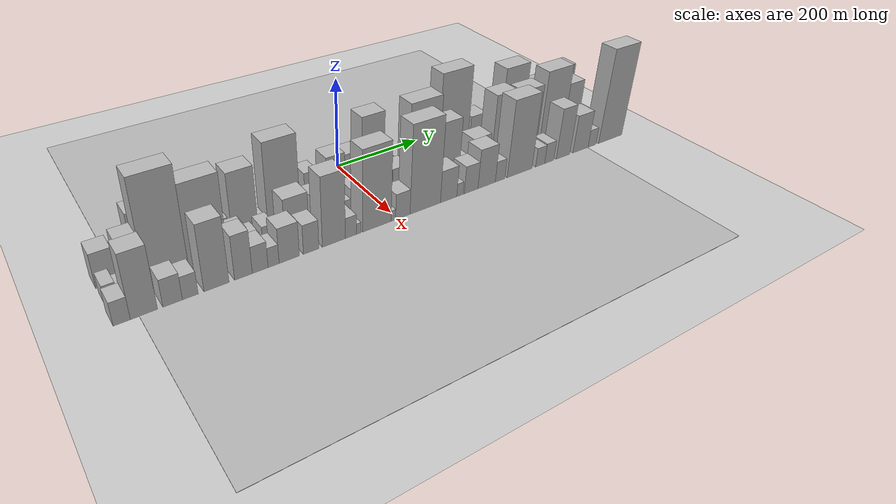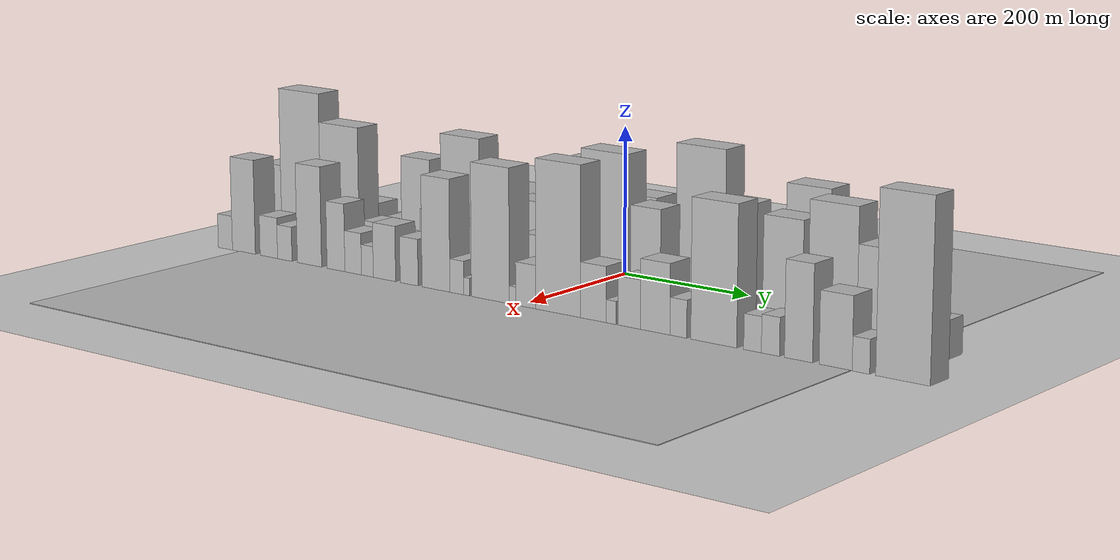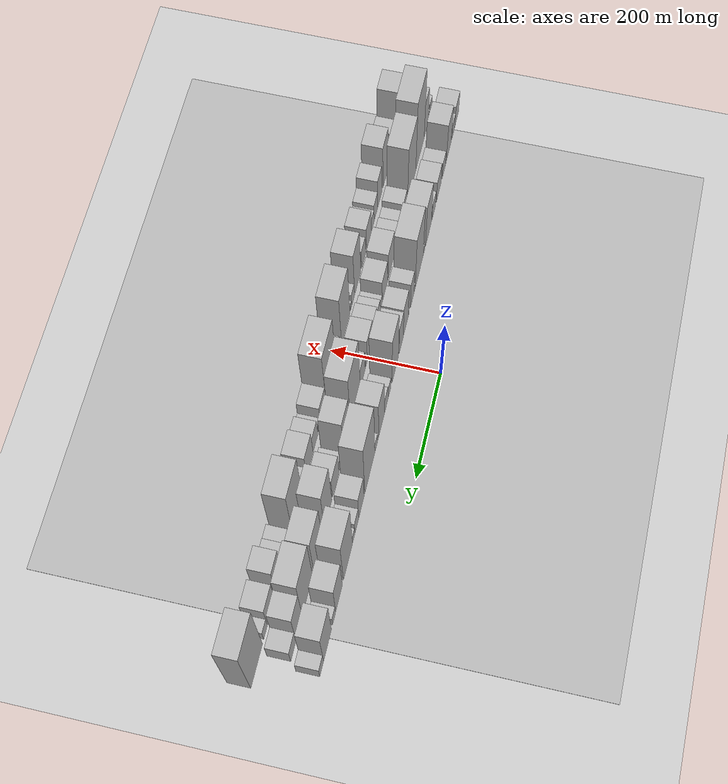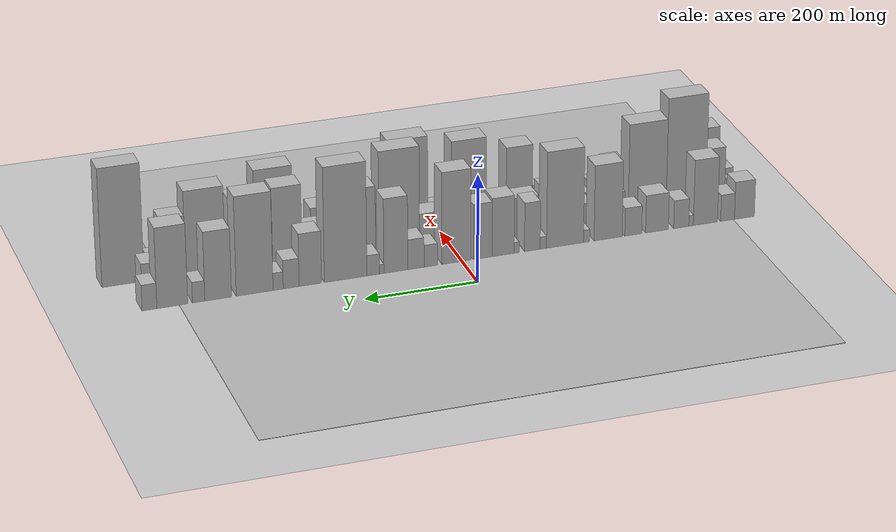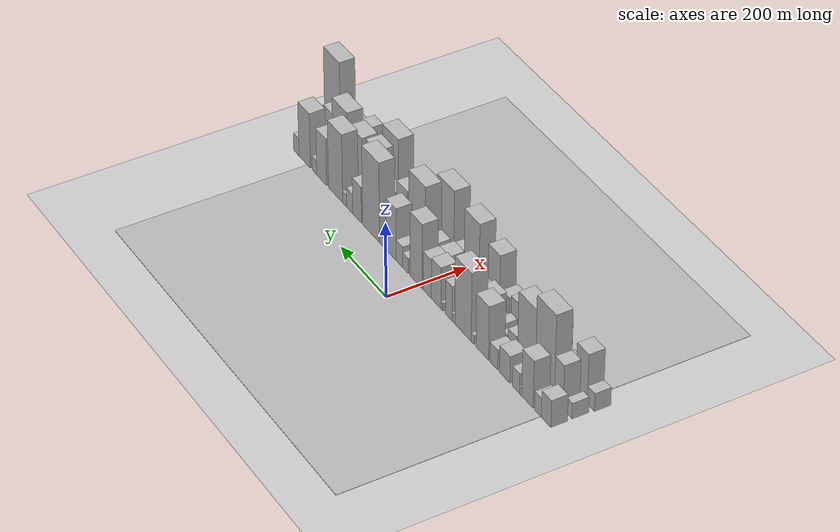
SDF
<?xml version="1.0" encoding="utf-8"?>

<sdf version="1.6">

   <world name="default">

      <gui fullscreen="0">

         <camera name="user_camera">

            <pose>-15 0 4.57585 0 0 0</pose>

            <view_controller>orbit</view_controller>

         </camera>

      </gui>

      <scene>

         <sky>

           <clouds>

             <speed>12</speed>

           </clouds>

         </sky>

         <ambient>0.4 0.4 0.4 1</ambient>

         <background>0.7 0.7 0.7 1</background>

         <shadows>1</shadows>

      </scene>

      <gravity>0 0 -9.8066</gravity>

      <magnetic_field>6e-06 2.3e-05 -4.2e-05</magnetic_field>

      <physics default="0" name="default_physics" type="ode">

         <ode>

            <solver>

               <type>quick</type>

               <iters>10</iters>

               <sor>1.0</sor>

               <use_dynamic_moi_rescaling>0</use_dynamic_moi_rescaling>

            </solver>

            <constraints>

               <cfm>0</cfm>

               <erp>0.2</erp>

               <contact_max_correcting_vel>100</contact_max_correcting_vel>

               <contact_surface_layer>0.001</contact_surface_layer>

            </constraints>

         </ode>

         <max_step_size>0.004</max_step_size>

         <real_time_factor>1</real_time_factor>

         <real_time_update_rate>250</real_time_update_rate>

      </physics>

      <light name="sun" type="directional">

         <cast_shadows>1</cast_shadows>

         <pose>0 0 10 0 0 0</pose>

         <diffuse>0.8 0.8 0.8 1</diffuse>

         <specular>0.2 0.2 0.2 1</specular>

         <attenuation>

            <range>1000</range>

            <constant>0.9</constant>

            <linear>0.01</linear>

            <quadratic>0.001</quadratic>

         </attenuation>

         <direction>-0.5 0.1 -0.9</direction>

      </light>

      <include>

         <name>ground_plane_1</name>

         <uri>model://HANNAS_ground_plane</uri>

         <pose>0 0 0  0 0 0</pose>

      </include>

      <include>

         <name>ground_plane_2</name>

         <uri>model://HANNAS_ground_plane</uri>

         <pose>100 0 0  0 0 0</pose>

      </include>

      <model name="building_1">

         <static>1</static>

         <pose frame="">100.0000 -521.2292 0 0.000000 0.000000 0.000000</pose>

         <link name="link">

            <pose frame="">0 0 36.00 0 0 0</pose>

            <collision name="collision">

               <geometry>

                  <box>

                     <size>40.0000 37.5416 72.0000</size>

                  </box>

               </geometry>

               <max_contacts>10</max_contacts>

               <surface>

                  <contact>

                     <ode/>

                  </contact>

                  <bounce/>

                  <friction>

                     <torsional>

                        <ode/>

                     </torsional>

                     <ode/>

                  </friction>

               </surface>

            </collision>

            <visual name="visual">

               <cast_shadows>0</cast_shadows>

               <geometry>

                  <box>

                     <size>40.0000 37.5416 72.0000</size>

                  </box>

               </geometry>

               <material>

                  <script>

                     <uri>model://HANNAS_wall/materials/scripts</uri>

                     <uri>model://HANNAS_wall/materials/textures</uri>

                     <name>vrc/HANNAS_wall</name>

                  </script>

               </material>

            </visual>

            <self_collide>0</self_collide>

            <enable_wind>0</enable_wind>

            <kinematic>0</kinematic>

         </link>

      </model>

      <model name="building_2">

         <static>1</static>

         <pose frame="">100.0000 -489.3952 0 0.000000 0.000000 0.000000</pose>

         <link name="link">

            <pose frame="">0 0 25.50 0 0 0</pose>

            <collision name="collision">

               <geometry>

                  <box>

                     <size>40.0000 26.1263 51.0000</size>

                  </box>

               </geometry>

               <max_contacts>10</max_contacts>

               <surface>

                  <contact>

                     <ode/>

                  </contact>

                  <bounce/>

                  <friction>

                     <torsional>

                        <ode/>

                     </torsional>

                     <ode/>

                  </friction>

               </surface>

            </collision>

            <visual name="visual">

               <cast_shadows>0</cast_shadows>

               <geometry>

                  <box>

                     <size>40.0000 26.1263 51.0000</size>

                  </box>

               </geometry>

               <material>

                  <script>

                     <uri>model://HANNAS_wall/materials/scripts</uri>

                     <uri>model://HANNAS_wall/materials/textures</uri>

                     <name>vrc/HANNAS_wall</name>

                  </script>

               </material>

            </visual>

            <self_collide>0</self_collide>

            <enable_wind>0</enable_wind>

            <kinematic>0</kinematic>

         </link>

      </model>

      <model name="building_3">

         <static>1</static>

         <pose frame="">100.0000 -447.6443 0 0.000000 0.000000 0.000000</pose>

         <link name="link">

            <pose frame="">0 0 63.00 0 0 0</pose>

            <collision name="collision">

               <geometry>

                  <box>

                     <size>40.0000 45.3757 126.0000</size>

                  </box>

               </geometry>

               <max_contacts>10</max_contacts>

               <surface>

                  <contact>

                     <ode/>

                  </contact>

                  <bounce/>

                  <friction>

                     <torsional>

                        <ode/>

                     </torsional>

                     <ode/>

                  </friction>

               </surface>

            </collision>

            <visual name="visual">

               <cast_shadows>0</cast_shadows>

               <geometry>

                  <box>

                     <size>40.0000 45.3757 126.0000</size>

                  </box>

               </geometry>

               <material>

                  <script>

                     <uri>model://HANNAS_wall/materials/scripts</uri>

                     <uri>model://HANNAS_wall/materials/textures</uri>

                     <name>vrc/HANNAS_wall</name>

                  </script>

               </material>

            </visual>

            <self_collide>0</self_collide>

            <enable_wind>0</enable_wind>

            <kinematic>0</kinematic>

         </link>

      </model>

      <model name="building_4">

         <static>1</static>

         <pose frame="">100.0000 -420.6477 0 0.000000 0.000000 0.000000</pose>

         <link name="link">

            <pose frame="">0 0 10.50 0 0 0</pose>

            <collision name="collision">

               <geometry>

                  <box>

                     <size>40.0000 8.6174 21.0000</size>

                  </box>

               </geometry>

               <max_contacts>10</max_contacts>

               <surface>

                  <contact>

                     <ode/>

                  </contact>

                  <bounce/>

                  <friction>

                     <torsional>

                        <ode/>

                     </torsional>

                     <ode/>

                  </friction>

               </surface>

            </collision>

            <visual name="visual">

               <cast_shadows>0</cast_shadows>

               <geometry>

                  <box>

                     <size>40.0000 8.6174 21.0000</size>

                  </box>

               </geometry>

               <material>

                  <script>

                     <uri>model://HANNAS_wall/materials/scripts</uri>

                     <uri>model://HANNAS_wall/materials/textures</uri>

                     <name>vrc/HANNAS_wall</name>

                  </script>

               </material>

            </visual>

            <self_collide>0</self_collide>

            <enable_wind>0</enable_wind>

            <kinematic>0</kinematic>

         </link>

      </model>

      <model name="building_5">

         <static>1</static>

         <pose frame="">100.0000 -402.2791 0 0.000000 0.000000 0.000000</pose>

         <link name="link">

            <pose frame="">0 0 27.00 0 0 0</pose>

            <collision name="collision">

               <geometry>

                  <box>

                     <size>40.0000 28.1198 54.0000</size>

                  </box>

               </geometry>

               <max_contacts>10</max_contacts>

               <surface>

                  <contact>

                     <ode/>

                  </contact>

                  <bounce/>

                  <friction>

                     <torsional>

                        <ode/>

                     </torsional>

                     <ode/>

                  </friction>

               </surface>

            </collision>

            <visual name="visual">

               <cast_shadows>0</cast_shadows>

               <geometry>

                  <box>

                     <size>40.0000 28.1198 54.0000</size>

                  </box>

               </geometry>

               <material>

                  <script>

                     <uri>model://HANNAS_wall/materials/scripts</uri>

                     <uri>model://HANNAS_wall/materials/textures</uri>

                     <name>vrc/HANNAS_wall</name>

                  </script>

               </material>

            </visual>

            <self_collide>0</self_collide>

            <enable_wind>0</enable_wind>

            <kinematic>0</kinematic>

         </link>

      </model>

      <model name="building_6">

         <static>1</static>

         <pose frame="">100.0000 -356.8882 0 0.000000 0.000000 0.000000</pose>

         <link name="link">

            <pose frame="">0 0 36.00 0 0 0</pose>

            <collision name="collision">

               <geometry>

                  <box>

                     <size>40.0000 42.6621 72.0000</size>

                  </box>

               </geometry>

               <max_contacts>10</max_contacts>

               <surface>

                  <contact>

                     <ode/>

                  </contact>

                  <bounce/>

                  <friction>

                     <torsional>

                        <ode/>

                     </torsional>

                     <ode/>

                  </friction>

               </surface>

            </collision>

            <visual name="visual">

               <cast_shadows>0</cast_shadows>

               <geometry>

                  <box>

                     <size>40.0000 42.6621 72.0000</size>

                  </box>

               </geometry>

               <material>

                  <script>

                     <uri>model://HANNAS_wall/materials/scripts</uri>

                     <uri>model://HANNAS_wall/materials/textures</uri>

                     <name>vrc/HANNAS_wall</name>

                  </script>

               </material>

            </visual>

            <self_collide>0</self_collide>

            <enable_wind>0</enable_wind>

            <kinematic>0</kinematic>

         </link>

      </model>

      <model name="building_7">

         <static>1</static>

         <pose frame="">100.0000 -312.8669 0 0.000000 0.000000 0.000000</pose>

         <link name="link">

            <pose frame="">0 0 27.00 0 0 0</pose>

            <collision name="collision">

               <geometry>

                  <box>

                     <size>40.0000 31.3804 54.0000</size>

                  </box>

               </geometry>

               <max_contacts>10</max_contacts>

               <surface>

                  <contact>

                     <ode/>

                  </contact>

                  <bounce/>

                  <friction>

                     <torsional>

                        <ode/>

                     </torsional>

                     <ode/>

                  </friction>

               </surface>

            </collision>

            <visual name="visual">

               <cast_shadows>0</cast_shadows>

               <geometry>

                  <box>

                     <size>40.0000 31.3804 54.0000</size>

                  </box>

               </geometry>

               <material>

                  <script>

                     <uri>model://HANNAS_wall/materials/scripts</uri>

                     <uri>model://HANNAS_wall/materials/textures</uri>

                     <name>vrc/HANNAS_wall</name>

                  </script>

               </material>

            </visual>

            <self_collide>0</self_collide>

            <enable_wind>0</enable_wind>

            <kinematic>0</kinematic>

         </link>

      </model>

      <model name="building_8">

         <static>1</static>

         <pose frame="">100.0000 -266.2269 0 0.000000 0.000000 0.000000</pose>

         <link name="link">

            <pose frame="">0 0 72.00 0 0 0</pose>

            <collision name="collision">

               <geometry>

                  <box>

                     <size>40.0000 51.8997 144.0000</size>

                  </box>

               </geometry>

               <max_contacts>10</max_contacts>

               <surface>

                  <contact>

                     <ode/>

                  </contact>

                  <bounce/>

                  <friction>

                     <torsional>

                        <ode/>

                     </torsional>

                     <ode/>

                  </friction>

               </surface>

            </collision>

            <visual name="visual">

               <cast_shadows>0</cast_shadows>

               <geometry>

                  <box>

                     <size>40.0000 51.8997 144.0000</size>

                  </box>

               </geometry>

               <material>

                  <script>

                     <uri>model://HANNAS_wall/materials/scripts</uri>

                     <uri>model://HANNAS_wall/materials/textures</uri>

                     <name>vrc/HANNAS_wall</name>

                  </script>

               </material>

            </visual>

            <self_collide>0</self_collide>

            <enable_wind>0</enable_wind>

            <kinematic>0</kinematic>

         </link>

      </model>

      <model name="building_9">

         <static>1</static>

         <pose frame="">100.0000 -226.4892 0 0.000000 0.000000 0.000000</pose>

         <link name="link">

            <pose frame="">0 0 12.00 0 0 0</pose>

            <collision name="collision">

               <geometry>

                  <box>

                     <size>40.0000 11.5759 24.0000</size>

                  </box>

               </geometry>

               <max_contacts>10</max_contacts>

               <surface>

                  <contact>

                     <ode/>

                  </contact>

                  <bounce/>

                  <friction>

                     <torsional>

                        <ode/>

                     </torsional>

                     <ode/>

                  </friction>

               </surface>

            </collision>

            <visual name="visual">

               <cast_shadows>0</cast_shadows>

               <geometry>

                  <box>

                     <size>40.0000 11.5759 24.0000</size>

                  </box>

               </geometry>

               <material>

                  <script>

                     <uri>model://HANNAS_wall/materials/scripts</uri>

                     <uri>model://HANNAS_wall/materials/textures</uri>

                     <name>vrc/HANNAS_wall</name>

                  </script>

               </material>

            </visual>

            <self_collide>0</self_collide>

            <enable_wind>0</enable_wind>

            <kinematic>0</kinematic>

         </link>

      </model>

      <model name="building_10">

         <static>1</static>

         <pose frame="">100.0000 -186.7829 0 0.000000 0.000000 0.000000</pose>

         <link name="link">

            <pose frame="">0 0 91.50 0 0 0</pose>

            <collision name="collision">

               <geometry>

                  <box>

                     <size>40.0000 67.8367 183.0000</size>

                  </box>

               </geometry>

               <max_contacts>10</max_contacts>

               <surface>

                  <contact>

                     <ode/>

                  </contact>

                  <bounce/>

                  <friction>

                     <torsional>

                        <ode/>

                     </torsional>

                     <ode/>

                  </friction>

               </surface>

            </collision>

            <visual name="visual">

               <cast_shadows>0</cast_shadows>

               <geometry>

                  <box>

                     <size>40.0000 67.8367 183.0000</size>

                  </box>

               </geometry>

               <material>

                  <script>

                     <uri>model://HANNAS_wall/materials/scripts</uri>

                     <uri>model://HANNAS_wall/materials/textures</uri>

                     <name>vrc/HANNAS_wall</name>

                  </script>

               </material>

            </visual>

            <self_collide>0</self_collide>

            <enable_wind>0</enable_wind>

            <kinematic>0</kinematic>

         </link>

      </model>

      <model name="building_11">

         <static>1</static>

         <pose frame="">100.0000 -147.0501 0 0.000000 0.000000 0.000000</pose>

         <link name="link">

            <pose frame="">0 0 12.00 0 0 0</pose>

            <collision name="collision">

               <geometry>

                  <box>

                     <size>40.0000 11.6288 24.0000</size>

                  </box>

               </geometry>

               <max_contacts>10</max_contacts>

               <surface>

                  <contact>

                     <ode/>

                  </contact>

                  <bounce/>

                  <friction>

                     <torsional>

                        <ode/>

                     </torsional>

                     <ode/>

                  </friction>

               </surface>

            </collision>

            <visual name="visual">

               <cast_shadows>0</cast_shadows>

               <geometry>

                  <box>

                     <size>40.0000 11.6288 24.0000</size>

                  </box>

               </geometry>

               <material>

                  <script>

                     <uri>model://HANNAS_wall/materials/scripts</uri>

                     <uri>model://HANNAS_wall/materials/textures</uri>

                     <name>vrc/HANNAS_wall</name>

                  </script>

               </material>

            </visual>

            <self_collide>0</self_collide>

            <enable_wind>0</enable_wind>

            <kinematic>0</kinematic>

         </link>

      </model>

      <model name="building_12">

         <static>1</static>

         <pose frame="">100.0000 -126.9637 0 0.000000 0.000000 0.000000</pose>

         <link name="link">

            <pose frame="">0 0 46.50 0 0 0</pose>

            <collision name="collision">

               <geometry>

                  <box>

                     <size>40.0000 28.5441 93.0000</size>

                  </box>

               </geometry>

               <max_contacts>10</max_contacts>

               <surface>

                  <contact>

                     <ode/>

                  </contact>

                  <bounce/>

                  <friction>

                     <torsional>

                        <ode/>

                     </torsional>

                     <ode/>

                  </friction>

               </surface>

            </collision>

            <visual name="visual">

               <cast_shadows>0</cast_shadows>

               <geometry>

                  <box>

                     <size>40.0000 28.5441 93.0000</size>

                  </box>

               </geometry>

               <material>

                  <script>

                     <uri>model://HANNAS_wall/materials/scripts</uri>

                     <uri>model://HANNAS_wall/materials/textures</uri>

                     <name>vrc/HANNAS_wall</name>

                  </script>

               </material>

            </visual>

            <self_collide>0</self_collide>

            <enable_wind>0</enable_wind>

            <kinematic>0</kinematic>

         </link>

      </model>

      <model name="building_13">

         <static>1</static>

         <pose frame="">100.0000 -98.3616 0 0.000000 0.000000 0.000000</pose>

         <link name="link">

            <pose frame="">0 0 10.50 0 0 0</pose>

            <collision name="collision">

               <geometry>

                  <box>

                     <size>40.0000 8.6600 21.0000</size>

                  </box>

               </geometry>

               <max_contacts>10</max_contacts>

               <surface>

                  <contact>

                     <ode/>

                  </contact>

                  <bounce/>

                  <friction>

                     <torsional>

                        <ode/>

                     </torsional>

                     <ode/>

                  </friction>

               </surface>

            </collision>

            <visual name="visual">

               <cast_shadows>0</cast_shadows>

               <geometry>

                  <box>

                     <size>40.0000 8.6600 21.0000</size>

                  </box>

               </geometry>

               <material>

                  <script>

                     <uri>model://HANNAS_wall/materials/scripts</uri>

                     <uri>model://HANNAS_wall/materials/textures</uri>

                     <name>vrc/HANNAS_wall</name>

                  </script>

               </material>

            </visual>

            <self_collide>0</self_collide>

            <enable_wind>0</enable_wind>

            <kinematic>0</kinematic>

         </link>

      </model>

      <model name="building_14">

         <static>1</static>

         <pose frame="">100.0000 -73.8813 0 0.000000 0.000000 0.000000</pose>

         <link name="link">

            <pose frame="">0 0 55.50 0 0 0</pose>

            <collision name="collision">

               <geometry>

                  <box>

                     <size>40.0000 40.3006 111.0000</size>

                  </box>

               </geometry>

               <max_contacts>10</max_contacts>

               <surface>

                  <contact>

                     <ode/>

                  </contact>

                  <bounce/>

                  <friction>

                     <torsional>

                        <ode/>

                     </torsional>

                     <ode/>

                  </friction>

               </surface>

            </collision>

            <visual name="visual">

               <cast_shadows>0</cast_shadows>

               <geometry>

                  <box>

                     <size>40.0000 40.3006 111.0000</size>

                  </box>

               </geometry>

               <material>

                  <script>

                     <uri>model://HANNAS_wall/materials/scripts</uri>

                     <uri>model://HANNAS_wall/materials/textures</uri>

                     <name>vrc/HANNAS_wall</name>

                  </script>

               </material>

            </visual>

            <self_collide>0</self_collide>

            <enable_wind>0</enable_wind>

            <kinematic>0</kinematic>

         </link>

      </model>

      <model name="building_15">

         <static>1</static>

         <pose frame="">100.0000 -36.5058 0 0.000000 0.000000 0.000000</pose>

         <link name="link">

            <pose frame="">0 0 52.50 0 0 0</pose>

            <collision name="collision">

               <geometry>

                  <box>

                     <size>40.0000 34.4504 105.0000</size>

                  </box>

               </geometry>

               <max_contacts>10</max_contacts>

               <surface>

                  <contact>

                     <ode/>

                  </contact>

                  <bounce/>

                  <friction>

                     <torsional>

                        <ode/>

                     </torsional>

                     <ode/>

                  </friction>

               </surface>

            </collision>

            <visual name="visual">

               <cast_shadows>0</cast_shadows>

               <geometry>

                  <box>

                     <size>40.0000 34.4504 105.0000</size>

                  </box>

               </geometry>

               <material>

                  <script>

                     <uri>model://HANNAS_wall/materials/scripts</uri>

                     <uri>model://HANNAS_wall/materials/textures</uri>

                     <name>vrc/HANNAS_wall</name>

                  </script>

               </material>

            </visual>

            <self_collide>0</self_collide>

            <enable_wind>0</enable_wind>

            <kinematic>0</kinematic>

         </link>

      </model>

      <model name="building_16">

         <static>1</static>

         <pose frame="">100.0000 10.8693 0 0.000000 0.000000 0.000000</pose>

         <link name="link">

            <pose frame="">0 0 87.00 0 0 0</pose>

            <collision name="collision">

               <geometry>

                  <box>

                     <size>40.0000 52.2997 174.0000</size>

                  </box>

               </geometry>

               <max_contacts>10</max_contacts>

               <surface>

                  <contact>

                     <ode/>

                  </contact>

                  <bounce/>

                  <friction>

                     <torsional>

                        <ode/>

                     </torsional>

                     <ode/>

                  </friction>

               </surface>

            </collision>

            <visual name="visual">

               <cast_shadows>0</cast_shadows>

               <geometry>

                  <box>

                     <size>40.0000 52.2997 174.0000</size>

                  </box>

               </geometry>

               <material>

                  <script>

                     <uri>model://HANNAS_wall/materials/scripts</uri>

                     <uri>model://HANNAS_wall/materials/textures</uri>

                     <name>vrc/HANNAS_wall</name>

                  </script>

               </material>

            </visual>

            <self_collide>0</self_collide>

            <enable_wind>0</enable_wind>

            <kinematic>0</kinematic>

         </link>

      </model>

      <model name="building_17">

         <static>1</static>

         <pose frame="">100.0000 56.9608 0 0.000000 0.000000 0.000000</pose>

         <link name="link">

            <pose frame="">0 0 21.00 0 0 0</pose>

            <collision name="collision">

               <geometry>

                  <box>

                     <size>40.0000 23.8834 42.0000</size>

                  </box>

               </geometry>

               <max_contacts>10</max_contacts>

               <surface>

                  <contact>

                     <ode/>

                  </contact>

                  <bounce/>

                  <friction>

                     <torsional>

                        <ode/>

                     </torsional>

                     <ode/>

                  </friction>

               </surface>

            </collision>

            <visual name="visual">

               <cast_shadows>0</cast_shadows>

               <geometry>

                  <box>

                     <size>40.0000 23.8834 42.0000</size>

                  </box>

               </geometry>

               <material>

                  <script>

                     <uri>model://HANNAS_wall/materials/scripts</uri>

                     <uri>model://HANNAS_wall/materials/textures</uri>

                     <name>vrc/HANNAS_wall</name>

                  </script>

               </material>

            </visual>

            <self_collide>0</self_collide>

            <enable_wind>0</enable_wind>

            <kinematic>0</kinematic>

         </link>

      </model>

      <model name="building_18">

         <static>1</static>

         <pose frame="">100.0000 83.5557 0 0.000000 0.000000 0.000000</pose>

         <link name="link">

            <pose frame="">0 0 28.50 0 0 0</pose>

            <collision name="collision">

               <geometry>

                  <box>

                     <size>40.0000 29.3063 57.0000</size>

                  </box>

               </geometry>

               <max_contacts>10</max_contacts>

               <surface>

                  <contact>

                     <ode/>

                  </contact>

                  <bounce/>

                  <friction>

                     <torsional>

                        <ode/>

                     </torsional>

                     <ode/>

                  </friction>

               </surface>

            </collision>

            <visual name="visual">

               <cast_shadows>0</cast_shadows>

               <geometry>

                  <box>

                     <size>40.0000 29.3063 57.0000</size>

                  </box>

               </geometry>

               <material>

                  <script>

                     <uri>model://HANNAS_wall/materials/scripts</uri>

                     <uri>model://HANNAS_wall/materials/textures</uri>

                     <name>vrc/HANNAS_wall</name>

                  </script>

               </material>

            </visual>

            <self_collide>0</self_collide>

            <enable_wind>0</enable_wind>

            <kinematic>0</kinematic>

         </link>

      </model>

      <model name="building_19">

         <static>1</static>

         <pose frame="">100.0000 119.6079 0 0.000000 0.000000 0.000000</pose>

         <link name="link">

            <pose frame="">0 0 70.50 0 0 0</pose>

            <collision name="collision">

               <geometry>

                  <box>

                     <size>40.0000 42.7981 141.0000</size>

                  </box>

               </geometry>

               <max_contacts>10</max_contacts>

               <surface>

                  <contact>

                     <ode/>

                  </contact>

                  <bounce/>

                  <friction>

                     <torsional>

                        <ode/>

                     </torsional>

                     <ode/>

                  </friction>

               </surface>

            </collision>

            <visual name="visual">

               <cast_shadows>0</cast_shadows>

               <geometry>

                  <box>

                     <size>40.0000 42.7981 141.0000</size>

                  </box>

               </geometry>

               <material>

                  <script>

                     <uri>model://HANNAS_wall/materials/scripts</uri>

                     <uri>model://HANNAS_wall/materials/textures</uri>

                     <name>vrc/HANNAS_wall</name>

                  </script>

               </material>

            </visual>

            <self_collide>0</self_collide>

            <enable_wind>0</enable_wind>

            <kinematic>0</kinematic>

         </link>

      </model>

      <model name="building_20">

         <static>1</static>

         <pose frame="">100.0000 144.9795 0 0.000000 0.000000 0.000000</pose>

         <link name="link">

            <pose frame="">0 0 9.00 0 0 0</pose>

            <collision name="collision">

               <geometry>

                  <box>

                     <size>40.0000 7.9451 18.0000</size>

                  </box>

               </geometry>

               <max_contacts>10</max_contacts>

               <surface>

                  <contact>

                     <ode/>

                  </contact>

                  <bounce/>

                  <friction>

                     <torsional>

                        <ode/>

                     </torsional>

                     <ode/>

                  </friction>

               </surface>

            </collision>

            <visual name="visual">

               <cast_shadows>0</cast_shadows>

               <geometry>

                  <box>

                     <size>40.0000 7.9451 18.0000</size>

                  </box>

               </geometry>

               <material>

                  <script>

                     <uri>model://HANNAS_wall/materials/scripts</uri>

                     <uri>model://HANNAS_wall/materials/textures</uri>

                     <name>vrc/HANNAS_wall</name>

                  </script>

               </material>

            </visual>

            <self_collide>0</self_collide>

            <enable_wind>0</enable_wind>

            <kinematic>0</kinematic>

         </link>

      </model>

      <model name="building_21">

         <static>1</static>

         <pose frame="">100.0000 160.0698 0 0.000000 0.000000 0.000000</pose>

         <link name="link">

            <pose frame="">0 0 19.50 0 0 0</pose>

            <collision name="collision">

               <geometry>

                  <box>

                     <size>40.0000 22.2356 39.0000</size>

                  </box>

               </geometry>

               <max_contacts>10</max_contacts>

               <surface>

                  <contact>

                     <ode/>

                  </contact>

                  <bounce/>

                  <friction>

                     <torsional>

                        <ode/>

                     </torsional>

                     <ode/>

                  </friction>

               </surface>

            </collision>

            <visual name="visual">

               <cast_shadows>0</cast_shadows>

               <geometry>

                  <box>

                     <size>40.0000 22.2356 39.0000</size>

                  </box>

               </geometry>

               <material>

                  <script>

                     <uri>model://HANNAS_wall/materials/scripts</uri>

                     <uri>model://HANNAS_wall/materials/textures</uri>

                     <name>vrc/HANNAS_wall</name>

                  </script>

               </material>

            </visual>

            <self_collide>0</self_collide>

            <enable_wind>0</enable_wind>

            <kinematic>0</kinematic>

         </link>

      </model>

      <model name="building_22">

         <static>1</static>

         <pose frame="">100.0000 208.9474 0 0.000000 0.000000 0.000000</pose>

         <link name="link">

            <pose frame="">0 0 108.00 0 0 0</pose>

            <collision name="collision">

               <geometry>

                  <box>

                     <size>40.0000 75.5195 216.0000</size>

                  </box>

               </geometry>

               <max_contacts>10</max_contacts>

               <surface>

                  <contact>

                     <ode/>

                  </contact>

                  <bounce/>

                  <friction>

                     <torsional>

                        <ode/>

                     </torsional>

                     <ode/>

                  </friction>

               </surface>

            </collision>

            <visual name="visual">

               <cast_shadows>0</cast_shadows>

               <geometry>

                  <box>

                     <size>40.0000 75.5195 216.0000</size>

                  </box>

               </geometry>

               <material>

                  <script>

                     <uri>model://HANNAS_wall/materials/scripts</uri>

                     <uri>model://HANNAS_wall/materials/textures</uri>

                     <name>vrc/HANNAS_wall</name>

                  </script>

               </material>

            </visual>

            <self_collide>0</self_collide>

            <enable_wind>0</enable_wind>

            <kinematic>0</kinematic>

         </link>

      </model>

      <model name="building_23">

         <static>1</static>

         <pose frame="">100.0000 271.4195 0 0.000000 0.000000 0.000000</pose>

         <link name="link">

            <pose frame="">0 0 49.50 0 0 0</pose>

            <collision name="collision">

               <geometry>

                  <box>

                     <size>40.0000 39.4247 99.0000</size>

                  </box>

               </geometry>

               <max_contacts>10</max_contacts>

               <surface>

                  <contact>

                     <ode/>

                  </contact>

                  <bounce/>

                  <friction>

                     <torsional>

                        <ode/>

                     </torsional>

                     <ode/>

                  </friction>

               </surface>

            </collision>

            <visual name="visual">

               <cast_shadows>0</cast_shadows>

               <geometry>

                  <box>

                     <size>40.0000 39.4247 99.0000</size>

                  </box>

               </geometry>

               <material>

                  <script>

                     <uri>model://HANNAS_wall/materials/scripts</uri>

                     <uri>model://HANNAS_wall/materials/textures</uri>

                     <name>vrc/HANNAS_wall</name>

                  </script>

               </material>

            </visual>

            <self_collide>0</self_collide>

            <enable_wind>0</enable_wind>

            <kinematic>0</kinematic>

         </link>

      </model>

      <model name="building_24">

         <static>1</static>

         <pose frame="">100.0000 305.1238 0 0.000000 0.000000 0.000000</pose>

         <link name="link">

            <pose frame="">0 0 27.00 0 0 0</pose>

            <collision name="collision">

               <geometry>

                  <box>

                     <size>40.0000 27.9839 54.0000</size>

                  </box>

               </geometry>

               <max_contacts>10</max_contacts>

               <surface>

                  <contact>

                     <ode/>

                  </contact>

                  <bounce/>

                  <friction>

                     <torsional>

                        <ode/>

                     </torsional>

                     <ode/>

                  </friction>

               </surface>

            </collision>

            <visual name="visual">

               <cast_shadows>0</cast_shadows>

               <geometry>

                  <box>

                     <size>40.0000 27.9839 54.0000</size>

                  </box>

               </geometry>

               <material>

                  <script>

                     <uri>model://HANNAS_wall/materials/scripts</uri>

                     <uri>model://HANNAS_wall/materials/textures</uri>

                     <name>vrc/HANNAS_wall</name>

                  </script>

               </material>

            </visual>

            <self_collide>0</self_collide>

            <enable_wind>0</enable_wind>

            <kinematic>0</kinematic>

         </link>

      </model>

      <model name="building_25">

         <static>1</static>

         <pose frame="">100.0000 328.0270 0 0.000000 0.000000 0.000000</pose>

         <link name="link">

            <pose frame="">0 0 16.50 0 0 0</pose>

            <collision name="collision">

               <geometry>

                  <box>

                     <size>40.0000 17.8224 33.0000</size>

                  </box>

               </geometry>

               <max_contacts>10</max_contacts>

               <surface>

                  <contact>

                     <ode/>

                  </contact>

                  <bounce/>

                  <friction>

                     <torsional>

                        <ode/>

                     </torsional>

                     <ode/>

                  </friction>

               </surface>

            </collision>

            <visual name="visual">

               <cast_shadows>0</cast_shadows>

               <geometry>

                  <box>

                     <size>40.0000 17.8224 33.0000</size>

                  </box>

               </geometry>

               <material>

                  <script>

                     <uri>model://HANNAS_wall/materials/scripts</uri>

                     <uri>model://HANNAS_wall/materials/textures</uri>

                     <name>vrc/HANNAS_wall</name>

                  </script>

               </material>

            </visual>

            <self_collide>0</self_collide>

            <enable_wind>0</enable_wind>

            <kinematic>0</kinematic>

         </link>

      </model>

      <model name="building_26">

         <static>1</static>

         <pose frame="">100.0000 369.1102 0 0.000000 0.000000 0.000000</pose>

         <link name="link">

            <pose frame="">0 0 93.00 0 0 0</pose>

            <collision name="collision">

               <geometry>

                  <box>

                     <size>40.0000 64.3441 186.0000</size>

                  </box>

               </geometry>

               <max_contacts>10</max_contacts>

               <surface>

                  <contact>

                     <ode/>

                  </contact>

                  <bounce/>

                  <friction>

                     <torsional>

                        <ode/>

                     </torsional>

                     <ode/>

                  </friction>

               </surface>

            </collision>

            <visual name="visual">

               <cast_shadows>0</cast_shadows>

               <geometry>

                  <box>

                     <size>40.0000 64.3441 186.0000</size>

                  </box>

               </geometry>

               <material>

                  <script>

                     <uri>model://HANNAS_wall/materials/scripts</uri>

                     <uri>model://HANNAS_wall/materials/textures</uri>

                     <name>vrc/HANNAS_wall</name>

                  </script>

               </material>

            </visual>

            <self_collide>0</self_collide>

            <enable_wind>0</enable_wind>

            <kinematic>0</kinematic>

         </link>

      </model>

      <model name="building_27">

         <static>1</static>

         <pose frame="">100.0000 432.4711 0 0.000000 0.000000 0.000000</pose>

         <link name="link">

            <pose frame="">0 0 64.50 0 0 0</pose>

            <collision name="collision">

               <geometry>

                  <box>

                     <size>40.0000 46.3777 129.0000</size>

                  </box>

               </geometry>

               <max_contacts>10</max_contacts>

               <surface>

                  <contact>

                     <ode/>

                  </contact>

                  <bounce/>

                  <friction>

                     <torsional>

                        <ode/>

                     </torsional>

                     <ode/>

                  </friction>

               </surface>

            </collision>

            <visual name="visual">

               <cast_shadows>0</cast_shadows>

               <geometry>

                  <box>

                     <size>40.0000 46.3777 129.0000</size>

                  </box>

               </geometry>

               <material>

                  <script>

                     <uri>model://HANNAS_wall/materials/scripts</uri>

                     <uri>model://HANNAS_wall/materials/textures</uri>

                     <name>vrc/HANNAS_wall</name>

                  </script>

               </material>

            </visual>

            <self_collide>0</self_collide>

            <enable_wind>0</enable_wind>

            <kinematic>0</kinematic>

         </link>

      </model>

      <model name="building_28">

         <static>1</static>

         <pose frame="">100.0000 466.4804 0 0.000000 0.000000 0.000000</pose>

         <link name="link">

            <pose frame="">0 0 19.50 0 0 0</pose>

            <collision name="collision">

               <geometry>

                  <box>

                     <size>40.0000 21.6409 39.0000</size>

                  </box>

               </geometry>

               <max_contacts>10</max_contacts>

               <surface>

                  <contact>

                     <ode/>

                  </contact>

                  <bounce/>

                  <friction>

                     <torsional>

                        <ode/>

                     </torsional>

                     <ode/>

                  </friction>

               </surface>

            </collision>

            <visual name="visual">

               <cast_shadows>0</cast_shadows>

               <geometry>

                  <box>

                     <size>40.0000 21.6409 39.0000</size>

                  </box>

               </geometry>

               <material>

                  <script>

                     <uri>model://HANNAS_wall/materials/scripts</uri>

                     <uri>model://HANNAS_wall/materials/textures</uri>

                     <name>vrc/HANNAS_wall</name>

                  </script>

               </material>

            </visual>

            <self_collide>0</self_collide>

            <enable_wind>0</enable_wind>

            <kinematic>0</kinematic>

         </link>

      </model>

      <model name="building_29">

         <static>1</static>

         <pose frame="">100.0000 511.8873 0 0.000000 0.000000 0.000000</pose>

         <link name="link">

            <pose frame="">0 0 75.00 0 0 0</pose>

            <collision name="collision">

               <geometry>

                  <box>

                     <size>40.0000 53.1729 150.0000</size>

                  </box>

               </geometry>

               <max_contacts>10</max_contacts>

               <surface>

                  <contact>

                     <ode/>

                  </contact>

                  <bounce/>

                  <friction>

                     <torsional>

                        <ode/>

                     </torsional>

                     <ode/>

                  </friction>

               </surface>

            </collision>

            <visual name="visual">

               <cast_shadows>0</cast_shadows>

               <geometry>

                  <box>

                     <size>40.0000 53.1729 150.0000</size>

                  </box>

               </geometry>

               <material>

                  <script>

                     <uri>model://HANNAS_wall/materials/scripts</uri>

                     <uri>model://HANNAS_wall/materials/textures</uri>

                     <name>vrc/HANNAS_wall</name>

                  </script>

               </material>

            </visual>

            <self_collide>0</self_collide>

            <enable_wind>0</enable_wind>

            <kinematic>0</kinematic>

         </link>

      </model>

      <model name="building_30">

         <static>1</static>

         <pose frame="">100.0000 551.2368 0 0.000000 0.000000 0.000000</pose>

         <link name="link">

            <pose frame="">0 0 24.00 0 0 0</pose>

            <collision name="collision">

               <geometry>

                  <box>

                     <size>40.0000 25.5261 48.0000</size>

                  </box>

               </geometry>

               <max_contacts>10</max_contacts>

               <surface>

                  <contact>

                     <ode/>

                  </contact>

                  <bounce/>

                  <friction>

                     <torsional>

                        <ode/>

                     </torsional>

                     <ode/>

                  </friction>

               </surface>

            </collision>

            <visual name="visual">

               <cast_shadows>0</cast_shadows>

               <geometry>

                  <box>

                     <size>40.0000 25.5261 48.0000</size>

                  </box>

               </geometry>

               <material>

                  <script>

                     <uri>model://HANNAS_wall/materials/scripts</uri>

                     <uri>model://HANNAS_wall/materials/textures</uri>

                     <name>vrc/HANNAS_wall</name>

                  </script>

               </material>

            </visual>

            <self_collide>0</self_collide>

            <enable_wind>0</enable_wind>

            <kinematic>0</kinematic>

         </link>

      </model>

      <model name="building_31">

         <static>1</static>

         <pose frame="">152.0000 -528.1778 0 0.000000 0.000000 0.000000</pose>

         <link name="link">

            <pose frame="">0 0 21.00 0 0 0</pose>

            <collision name="collision">

               <geometry>

                  <box>

                     <size>40.0000 21.6443 42.0000</size>

                  </box>

               </geometry>

               <max_contacts>10</max_contacts>

               <surface>

                  <contact>

                     <ode/>

                  </contact>

                  <bounce/>

                  <friction>

                     <torsional>

                        <ode/>

                     </torsional>

                     <ode/>

                  </friction>

               </surface>

            </collision>

            <visual name="visual">

               <cast_shadows>0</cast_shadows>

               <geometry>

                  <box>

                     <size>40.0000 21.6443 42.0000</size>

                  </box>

               </geometry>

               <material>

                  <script>

                     <uri>model://HANNAS_wall/materials/scripts</uri>

                     <uri>model://HANNAS_wall/materials/textures</uri>

                     <name>vrc/HANNAS_wall</name>

                  </script>

               </material>

            </visual>

            <self_collide>0</self_collide>

            <enable_wind>0</enable_wind>

            <kinematic>0</kinematic>

         </link>

      </model>

      <model name="building_32">

         <static>1</static>

         <pose frame="">152.0000 -510.8541 0 0.000000 0.000000 0.000000</pose>

         <link name="link">

            <pose frame="">0 0 13.50 0 0 0</pose>

            <collision name="collision">

               <geometry>

                  <box>

                     <size>40.0000 13.0031 27.0000</size>

                  </box>

               </geometry>

               <max_contacts>10</max_contacts>

               <surface>

                  <contact>

                     <ode/>

                  </contact>

                  <bounce/>

                  <friction>

                     <torsional>

                        <ode/>

                     </torsional>

                     <ode/>

                  </friction>

               </surface>

            </collision>

            <visual name="visual">

               <cast_shadows>0</cast_shadows>

               <geometry>

                  <box>

                     <size>40.0000 13.0031 27.0000</size>

                  </box>

               </geometry>

               <material>

                  <script>

                     <uri>model://HANNAS_wall/materials/scripts</uri>

                     <uri>model://HANNAS_wall/materials/textures</uri>

                     <name>vrc/HANNAS_wall</name>

                  </script>

               </material>

            </visual>

            <self_collide>0</self_collide>

            <enable_wind>0</enable_wind>

            <kinematic>0</kinematic>

         </link>

      </model>

      <model name="building_33">

         <static>1</static>

         <pose frame="">152.0000 -486.6505 0 0.000000 0.000000 0.000000</pose>

         <link name="link">

            <pose frame="">0 0 58.50 0 0 0</pose>

            <collision name="collision">

               <geometry>

                  <box>

                     <size>40.0000 35.4040 117.0000</size>

                  </box>

               </geometry>

               <max_contacts>10</max_contacts>

               <surface>

                  <contact>

                     <ode/>

                  </contact>

                  <bounce/>

                  <friction>

                     <torsional>

                        <ode/>

                     </torsional>

                     <ode/>

                  </friction>

               </surface>

            </collision>

            <visual name="visual">

               <cast_shadows>0</cast_shadows>

               <geometry>

                  <box>

                     <size>40.0000 35.4040 117.0000</size>

                  </box>

               </geometry>

               <material>

                  <script>

                     <uri>model://HANNAS_wall/materials/scripts</uri>

                     <uri>model://HANNAS_wall/materials/textures</uri>

                     <name>vrc/HANNAS_wall</name>

                  </script>

               </material>

            </visual>

            <self_collide>0</self_collide>

            <enable_wind>0</enable_wind>

            <kinematic>0</kinematic>

         </link>

      </model>

      <model name="building_34">

         <static>1</static>

         <pose frame="">152.0000 -431.5255 0 0.000000 0.000000 0.000000</pose>

         <link name="link">

            <pose frame="">0 0 112.50 0 0 0</pose>

            <collision name="collision">

               <geometry>

                  <box>

                     <size>40.0000 74.8459 225.0000</size>

                  </box>

               </geometry>

               <max_contacts>10</max_contacts>

               <surface>

                  <contact>

                     <ode/>

                  </contact>

                  <bounce/>

                  <friction>

                     <torsional>

                        <ode/>

                     </torsional>

                     <ode/>

                  </friction>

               </surface>

            </collision>

            <visual name="visual">

               <cast_shadows>0</cast_shadows>

               <geometry>

                  <box>

                     <size>40.0000 74.8459 225.0000</size>

                  </box>

               </geometry>

               <material>

                  <script>

                     <uri>model://HANNAS_wall/materials/scripts</uri>

                     <uri>model://HANNAS_wall/materials/textures</uri>

                     <name>vrc/HANNAS_wall</name>

                  </script>

               </material>

            </visual>

            <self_collide>0</self_collide>

            <enable_wind>0</enable_wind>

            <kinematic>0</kinematic>

         </link>

      </model>

      <model name="building_35">

         <static>1</static>

         <pose frame="">152.0000 -358.5160 0 0.000000 0.000000 0.000000</pose>

         <link name="link">

            <pose frame="">0 0 93.00 0 0 0</pose>

            <collision name="collision">

               <geometry>

                  <box>

                     <size>40.0000 71.1732 186.0000</size>

                  </box>

               </geometry>

               <max_contacts>10</max_contacts>

               <surface>

                  <contact>

                     <ode/>

                  </contact>

                  <bounce/>

                  <friction>

                     <torsional>

                        <ode/>

                     </torsional>

                     <ode/>

                  </friction>

               </surface>

            </collision>

            <visual name="visual">

               <cast_shadows>0</cast_shadows>

               <geometry>

                  <box>

                     <size>40.0000 71.1732 186.0000</size>

                  </box>

               </geometry>

               <material>

                  <script>

                     <uri>model://HANNAS_wall/materials/scripts</uri>

                     <uri>model://HANNAS_wall/materials/textures</uri>

                     <name>vrc/HANNAS_wall</name>

                  </script>

               </material>

            </visual>

            <self_collide>0</self_collide>

            <enable_wind>0</enable_wind>

            <kinematic>0</kinematic>

         </link>

      </model>

      <model name="building_36">

         <static>1</static>

         <pose frame="">152.0000 -300.5440 0 0.000000 0.000000 0.000000</pose>

         <link name="link">

            <pose frame="">0 0 30.00 0 0 0</pose>

            <collision name="collision">

               <geometry>

                  <box>

                     <size>40.0000 32.7709 60.0000</size>

                  </box>

               </geometry>

               <max_contacts>10</max_contacts>

               <surface>

                  <contact>

                     <ode/>

                  </contact>

                  <bounce/>

                  <friction>

                     <torsional>

                        <ode/>

                     </torsional>

                     <ode/>

                  </friction>

               </surface>

            </collision>

            <visual name="visual">

               <cast_shadows>0</cast_shadows>

               <geometry>

                  <box>

                     <size>40.0000 32.7709 60.0000</size>

                  </box>

               </geometry>

               <material>

                  <script>

                     <uri>model://HANNAS_wall/materials/scripts</uri>

                     <uri>model://HANNAS_wall/materials/textures</uri>

                     <name>vrc/HANNAS_wall</name>

                  </script>

               </material>

            </visual>

            <self_collide>0</self_collide>

            <enable_wind>0</enable_wind>

            <kinematic>0</kinematic>

         </link>

      </model>

      <model name="building_37">

         <static>1</static>

         <pose frame="">152.0000 -272.6185 0 0.000000 0.000000 0.000000</pose>

         <link name="link">

            <pose frame="">0 0 19.50 0 0 0</pose>

            <collision name="collision">

               <geometry>

                  <box>

                     <size>40.0000 23.0800 39.0000</size>

                  </box>

               </geometry>

               <max_contacts>10</max_contacts>

               <surface>

                  <contact>

                     <ode/>

                  </contact>

                  <bounce/>

                  <friction>

                     <torsional>

                        <ode/>

                     </torsional>

                     <ode/>

                  </friction>

               </surface>

            </collision>

            <visual name="visual">

               <cast_shadows>0</cast_shadows>

               <geometry>

                  <box>

                     <size>40.0000 23.0800 39.0000</size>

                  </box>

               </geometry>

               <material>

                  <script>

                     <uri>model://HANNAS_wall/materials/scripts</uri>

                     <uri>model://HANNAS_wall/materials/textures</uri>

                     <name>vrc/HANNAS_wall</name>

                  </script>

               </material>

            </visual>

            <self_collide>0</self_collide>

            <enable_wind>0</enable_wind>

            <kinematic>0</kinematic>

         </link>

      </model>

      <model name="building_38">

         <static>1</static>

         <pose frame="">152.0000 -243.2414 0 0.000000 0.000000 0.000000</pose>

         <link name="link">

            <pose frame="">0 0 24.00 0 0 0</pose>

            <collision name="collision">

               <geometry>

                  <box>

                     <size>40.0000 25.6743 48.0000</size>

                  </box>

               </geometry>

               <max_contacts>10</max_contacts>

               <surface>

                  <contact>

                     <ode/>

                  </contact>

                  <bounce/>

                  <friction>

                     <torsional>

                        <ode/>

                     </torsional>

                     <ode/>

                  </friction>

               </surface>

            </collision>

            <visual name="visual">

               <cast_shadows>0</cast_shadows>

               <geometry>

                  <box>

                     <size>40.0000 25.6743 48.0000</size>

                  </box>

               </geometry>

               <material>

                  <script>

                     <uri>model://HANNAS_wall/materials/scripts</uri>

                     <uri>model://HANNAS_wall/materials/textures</uri>

                     <name>vrc/HANNAS_wall</name>

                  </script>

               </material>

            </visual>

            <self_collide>0</self_collide>

            <enable_wind>0</enable_wind>

            <kinematic>0</kinematic>

         </link>

      </model>

      <model name="building_39">

         <static>1</static>

         <pose frame="">152.0000 -221.3581 0 0.000000 0.000000 0.000000</pose>

         <link name="link">

            <pose frame="">0 0 18.00 0 0 0</pose>

            <collision name="collision">

               <geometry>

                  <box>

                     <size>40.0000 18.0922 36.0000</size>

                  </box>

               </geometry>

               <max_contacts>10</max_contacts>

               <surface>

                  <contact>

                     <ode/>

                  </contact>

                  <bounce/>

                  <friction>

                     <torsional>

                        <ode/>

                     </torsional>

                     <ode/>

                  </friction>

               </surface>

            </collision>

            <visual name="visual">

               <cast_shadows>0</cast_shadows>

               <geometry>

                  <box>

                     <size>40.0000 18.0922 36.0000</size>

                  </box>

               </geometry>

               <material>

                  <script>

                     <uri>model://HANNAS_wall/materials/scripts</uri>

                     <uri>model://HANNAS_wall/materials/textures</uri>

                     <name>vrc/HANNAS_wall</name>

                  </script>

               </material>

            </visual>

            <self_collide>0</self_collide>

            <enable_wind>0</enable_wind>

            <kinematic>0</kinematic>

         </link>

      </model>

      <model name="building_40">

         <static>1</static>

         <pose frame="">152.0000 -187.5275 0 0.000000 0.000000 0.000000</pose>

         <link name="link">

            <pose frame="">0 0 45.00 0 0 0</pose>

            <collision name="collision">

               <geometry>

                  <box>

                     <size>40.0000 49.5690 90.0000</size>

                  </box>

               </geometry>

               <max_contacts>10</max_contacts>

               <surface>

                  <contact>

                     <ode/>

                  </contact>

                  <bounce/>

                  <friction>

                     <torsional>

                        <ode/>

                     </torsional>

                     <ode/>

                  </friction>

               </surface>

            </collision>

            <visual name="visual">

               <cast_shadows>0</cast_shadows>

               <geometry>

                  <box>

                     <size>40.0000 49.5690 90.0000</size>

                  </box>

               </geometry>

               <material>

                  <script>

                     <uri>model://HANNAS_wall/materials/scripts</uri>

                     <uri>model://HANNAS_wall/materials/textures</uri>

                     <name>vrc/HANNAS_wall</name>

                  </script>

               </material>

            </visual>

            <self_collide>0</self_collide>

            <enable_wind>0</enable_wind>

            <kinematic>0</kinematic>

         </link>

      </model>

      <model name="building_41">

         <static>1</static>

         <pose frame="">152.0000 -159.6810 0 0.000000 0.000000 0.000000</pose>

         <link name="link">

            <pose frame="">0 0 7.50 0 0 0</pose>

            <collision name="collision">

               <geometry>

                  <box>

                     <size>40.0000 6.1241 15.0000</size>

                  </box>

               </geometry>

               <max_contacts>10</max_contacts>

               <surface>

                  <contact>

                     <ode/>

                  </contact>

                  <bounce/>

                  <friction>

                     <torsional>

                        <ode/>

                     </torsional>

                     <ode/>

                  </friction>

               </surface>

            </collision>

            <visual name="visual">

               <cast_shadows>0</cast_shadows>

               <geometry>

                  <box>

                     <size>40.0000 6.1241 15.0000</size>

                  </box>

               </geometry>

               <material>

                  <script>

                     <uri>model://HANNAS_wall/materials/scripts</uri>

                     <uri>model://HANNAS_wall/materials/textures</uri>

                     <name>vrc/HANNAS_wall</name>

                  </script>

               </material>

            </visual>

            <self_collide>0</self_collide>

            <enable_wind>0</enable_wind>

            <kinematic>0</kinematic>

         </link>

      </model>

      <model name="building_42">

         <static>1</static>

         <pose frame="">152.0000 -134.6582 0 0.000000 0.000000 0.000000</pose>

         <link name="link">

            <pose frame="">0 0 39.00 0 0 0</pose>

            <collision name="collision">

               <geometry>

                  <box>

                     <size>40.0000 43.9215 78.0000</size>

                  </box>

               </geometry>

               <max_contacts>10</max_contacts>

               <surface>

                  <contact>

                     <ode/>

                  </contact>

                  <bounce/>

                  <friction>

                     <torsional>

                        <ode/>

                     </torsional>

                     <ode/>

                  </friction>

               </surface>

            </collision>

            <visual name="visual">

               <cast_shadows>0</cast_shadows>

               <geometry>

                  <box>

                     <size>40.0000 43.9215 78.0000</size>

                  </box>

               </geometry>

               <material>

                  <script>

                     <uri>model://HANNAS_wall/materials/scripts</uri>

                     <uri>model://HANNAS_wall/materials/textures</uri>

                     <name>vrc/HANNAS_wall</name>

                  </script>

               </material>

            </visual>

            <self_collide>0</self_collide>

            <enable_wind>0</enable_wind>

            <kinematic>0</kinematic>

         </link>

      </model>

      <model name="building_43">

         <static>1</static>

         <pose frame="">152.0000 -105.0419 0 0.000000 0.000000 0.000000</pose>

         <link name="link">

            <pose frame="">0 0 15.00 0 0 0</pose>

            <collision name="collision">

               <geometry>

                  <box>

                     <size>40.0000 15.3110 30.0000</size>

                  </box>

               </geometry>

               <max_contacts>10</max_contacts>

               <surface>

                  <contact>

                     <ode/>

                  </contact>

                  <bounce/>

                  <friction>

                     <torsional>

                        <ode/>

                     </torsional>

                     <ode/>

                  </friction>

               </surface>

            </collision>

            <visual name="visual">

               <cast_shadows>0</cast_shadows>

               <geometry>

                  <box>

                     <size>40.0000 15.3110 30.0000</size>

                  </box>

               </geometry>

               <material>

                  <script>

                     <uri>model://HANNAS_wall/materials/scripts</uri>

                     <uri>model://HANNAS_wall/materials/textures</uri>

                     <name>vrc/HANNAS_wall</name>

                  </script>

               </material>

            </visual>

            <self_collide>0</self_collide>

            <enable_wind>0</enable_wind>

            <kinematic>0</kinematic>

         </link>

      </model>

      <model name="building_44">

         <static>1</static>

         <pose frame="">152.0000 -84.9312 0 0.000000 0.000000 0.000000</pose>

         <link name="link">

            <pose frame="">0 0 21.00 0 0 0</pose>

            <collision name="collision">

               <geometry>

                  <box>

                     <size>40.0000 24.9103 42.0000</size>

                  </box>

               </geometry>

               <max_contacts>10</max_contacts>

               <surface>

                  <contact>

                     <ode/>

                  </contact>

                  <bounce/>

                  <friction>

                     <torsional>

                        <ode/>

                     </torsional>

                     <ode/>

                  </friction>

               </surface>

            </collision>

            <visual name="visual">

               <cast_shadows>0</cast_shadows>

               <geometry>

                  <box>

                     <size>40.0000 24.9103 42.0000</size>

                  </box>

               </geometry>

               <material>

                  <script>

                     <uri>model://HANNAS_wall/materials/scripts</uri>

                     <uri>model://HANNAS_wall/materials/textures</uri>

                     <name>vrc/HANNAS_wall</name>

                  </script>

               </material>

            </visual>

            <self_collide>0</self_collide>

            <enable_wind>0</enable_wind>

            <kinematic>0</kinematic>

         </link>

      </model>

      <model name="building_45">

         <static>1</static>

         <pose frame="">152.0000 -56.4137 0 0.000000 0.000000 0.000000</pose>

         <link name="link">

            <pose frame="">0 0 31.50 0 0 0</pose>

            <collision name="collision">

               <geometry>

                  <box>

                     <size>40.0000 32.1248 63.0000</size>

                  </box>

               </geometry>

               <max_contacts>10</max_contacts>

               <surface>

                  <contact>

                     <ode/>

                  </contact>

                  <bounce/>

                  <friction>

                     <torsional>

                        <ode/>

                     </torsional>

                     <ode/>

                  </friction>

               </surface>

            </collision>

            <visual name="visual">

               <cast_shadows>0</cast_shadows>

               <geometry>

                  <box>

                     <size>40.0000 32.1248 63.0000</size>

                  </box>

               </geometry>

               <material>

                  <script>

                     <uri>model://HANNAS_wall/materials/scripts</uri>

                     <uri>model://HANNAS_wall/materials/textures</uri>

                     <name>vrc/HANNAS_wall</name>

                  </script>

               </material>

            </visual>

            <self_collide>0</self_collide>

            <enable_wind>0</enable_wind>

            <kinematic>0</kinematic>

         </link>

      </model>

      <model name="building_46">

         <static>1</static>

         <pose frame="">152.0000 -15.9616 0 0.000000 0.000000 0.000000</pose>

         <link name="link">

            <pose frame="">0 0 40.50 0 0 0</pose>

            <collision name="collision">

               <geometry>

                  <box>

                     <size>40.0000 42.7795 81.0000</size>

                  </box>

               </geometry>

               <max_contacts>10</max_contacts>

               <surface>

                  <contact>

                     <ode/>

                  </contact>

                  <bounce/>

                  <friction>

                     <torsional>

                        <ode/>

                     </torsional>

                     <ode/>

                  </friction>

               </surface>

            </collision>

            <visual name="visual">

               <cast_shadows>0</cast_shadows>

               <geometry>

                  <box>

                     <size>40.0000 42.7795 81.0000</size>

                  </box>

               </geometry>

               <material>

                  <script>

                     <uri>model://HANNAS_wall/materials/scripts</uri>

                     <uri>model://HANNAS_wall/materials/textures</uri>

                     <name>vrc/HANNAS_wall</name>

                  </script>

               </material>

            </visual>

            <self_collide>0</self_collide>

            <enable_wind>0</enable_wind>

            <kinematic>0</kinematic>

         </link>

      </model>

      <model name="building_47">

         <static>1</static>

         <pose frame="">152.0000 11.9285 0 0.000000 0.000000 0.000000</pose>

         <link name="link">

            <pose frame="">0 0 13.50 0 0 0</pose>

            <collision name="collision">

               <geometry>

                  <box>

                     <size>40.0000 13.0005 27.0000</size>

                  </box>

               </geometry>

               <max_contacts>10</max_contacts>

               <surface>

                  <contact>

                     <ode/>

                  </contact>

                  <bounce/>

                  <friction>

                     <torsional>

                        <ode/>

                     </torsional>

                     <ode/>

                  </friction>

               </surface>

            </collision>

            <visual name="visual">

               <cast_shadows>0</cast_shadows>

               <geometry>

                  <box>

                     <size>40.0000 13.0005 27.0000</size>

                  </box>

               </geometry>

               <material>

                  <script>

                     <uri>model://HANNAS_wall/materials/scripts</uri>

                     <uri>model://HANNAS_wall/materials/textures</uri>

                     <name>vrc/HANNAS_wall</name>

                  </script>

               </material>

            </visual>

            <self_collide>0</self_collide>

            <enable_wind>0</enable_wind>

            <kinematic>0</kinematic>

         </link>

      </model>

      <model name="building_48">

         <static>1</static>

         <pose frame="">152.0000 40.6901 0 0.000000 0.000000 0.000000</pose>

         <link name="link">

            <pose frame="">0 0 37.50 0 0 0</pose>

            <collision name="collision">

               <geometry>

                  <box>

                     <size>40.0000 38.5228 75.0000</size>

                  </box>

               </geometry>

               <max_contacts>10</max_contacts>

               <surface>

                  <contact>

                     <ode/>

                  </contact>

                  <bounce/>

                  <friction>

                     <torsional>

                        <ode/>

                     </torsional>

                     <ode/>

                  </friction>

               </surface>

            </collision>

            <visual name="visual">

               <cast_shadows>0</cast_shadows>

               <geometry>

                  <box>

                     <size>40.0000 38.5228 75.0000</size>

                  </box>

               </geometry>

               <material>

                  <script>

                     <uri>model://HANNAS_wall/materials/scripts</uri>

                     <uri>model://HANNAS_wall/materials/textures</uri>

                     <name>vrc/HANNAS_wall</name>

                  </script>

               </material>

            </visual>

            <self_collide>0</self_collide>

            <enable_wind>0</enable_wind>

            <kinematic>0</kinematic>

         </link>

      </model>

      <model name="building_49">

         <static>1</static>

         <pose frame="">152.0000 96.4202 0 0.000000 0.000000 0.000000</pose>

         <link name="link">

            <pose frame="">0 0 102.00 0 0 0</pose>

            <collision name="collision">

               <geometry>

                  <box>

                     <size>40.0000 72.9375 204.0000</size>

                  </box>

               </geometry>

               <max_contacts>10</max_contacts>

               <surface>

                  <contact>

                     <ode/>

                  </contact>

                  <bounce/>

                  <friction>

                     <torsional>

                        <ode/>

                     </torsional>

                     <ode/>

                  </friction>

               </surface>

            </collision>

            <visual name="visual">

               <cast_shadows>0</cast_shadows>

               <geometry>

                  <box>

                     <size>40.0000 72.9375 204.0000</size>

                  </box>

               </geometry>

               <material>

                  <script>

                     <uri>model://HANNAS_wall/materials/scripts</uri>

                     <uri>model://HANNAS_wall/materials/textures</uri>

                     <name>vrc/HANNAS_wall</name>

                  </script>

               </material>

            </visual>

            <self_collide>0</self_collide>

            <enable_wind>0</enable_wind>

            <kinematic>0</kinematic>

         </link>

      </model>

      <model name="building_50">

         <static>1</static>

         <pose frame="">152.0000 162.1256 0 0.000000 0.000000 0.000000</pose>

         <link name="link">

            <pose frame="">0 0 70.50 0 0 0</pose>

            <collision name="collision">

               <geometry>

                  <box>

                     <size>40.0000 46.4732 141.0000</size>

                  </box>

               </geometry>

               <max_contacts>10</max_contacts>

               <surface>

                  <contact>

                     <ode/>

                  </contact>

                  <bounce/>

                  <friction>

                     <torsional>

                        <ode/>

                     </torsional>

                     <ode/>

                  </friction>

               </surface>

            </collision>

            <visual name="visual">

               <cast_shadows>0</cast_shadows>

               <geometry>

                  <box>

                     <size>40.0000 46.4732 141.0000</size>

                  </box>

               </geometry>

               <material>

                  <script>

                     <uri>model://HANNAS_wall/materials/scripts</uri>

                     <uri>model://HANNAS_wall/materials/textures</uri>

                     <name>vrc/HANNAS_wall</name>

                  </script>

               </material>

            </visual>

            <self_collide>0</self_collide>

            <enable_wind>0</enable_wind>

            <kinematic>0</kinematic>

         </link>

      </model>

      <model name="building_51">

         <static>1</static>

         <pose frame="">152.0000 206.7316 0 0.000000 0.000000 0.000000</pose>

         <link name="link">

            <pose frame="">0 0 19.50 0 0 0</pose>

            <collision name="collision">

               <geometry>

                  <box>

                     <size>40.0000 22.7387 39.0000</size>

                  </box>

               </geometry>

               <max_contacts>10</max_contacts>

               <surface>

                  <contact>

                     <ode/>

                  </contact>

                  <bounce/>

                  <friction>

                     <torsional>

                        <ode/>

                     </torsional>

                     <ode/>

                  </friction>

               </surface>

            </collision>

            <visual name="visual">

               <cast_shadows>0</cast_shadows>

               <geometry>

                  <box>

                     <size>40.0000 22.7387 39.0000</size>

                  </box>

               </geometry>

               <material>

                  <script>

                     <uri>model://HANNAS_wall/materials/scripts</uri>

                     <uri>model://HANNAS_wall/materials/textures</uri>

                     <name>vrc/HANNAS_wall</name>

                  </script>

               </material>

            </visual>

            <self_collide>0</self_collide>

            <enable_wind>0</enable_wind>

            <kinematic>0</kinematic>

         </link>

      </model>

      <model name="building_52">

         <static>1</static>

         <pose frame="">152.0000 241.5072 0 0.000000 0.000000 0.000000</pose>

         <link name="link">

            <pose frame="">0 0 40.50 0 0 0</pose>

            <collision name="collision">

               <geometry>

                  <box>

                     <size>40.0000 46.8126 81.0000</size>

                  </box>

               </geometry>

               <max_contacts>10</max_contacts>

               <surface>

                  <contact>

                     <ode/>

                  </contact>

                  <bounce/>

                  <friction>

                     <torsional>

                        <ode/>

                     </torsional>

                     <ode/>

                  </friction>

               </surface>

            </collision>

            <visual name="visual">

               <cast_shadows>0</cast_shadows>

               <geometry>

                  <box>

                     <size>40.0000 46.8126 81.0000</size>

                  </box>

               </geometry>

               <material>

                  <script>

                     <uri>model://HANNAS_wall/materials/scripts</uri>

                     <uri>model://HANNAS_wall/materials/textures</uri>

                     <name>vrc/HANNAS_wall</name>

                  </script>

               </material>

            </visual>

            <self_collide>0</self_collide>

            <enable_wind>0</enable_wind>

            <kinematic>0</kinematic>

         </link>

      </model>

      <model name="building_53">

         <static>1</static>

         <pose frame="">152.0000 295.9425 0 0.000000 0.000000 0.000000</pose>

         <link name="link">

            <pose frame="">0 0 82.50 0 0 0</pose>

            <collision name="collision">

               <geometry>

                  <box>

                     <size>40.0000 52.0578 165.0000</size>

                  </box>

               </geometry>

               <max_contacts>10</max_contacts>

               <surface>

                  <contact>

                     <ode/>

                  </contact>

                  <bounce/>

                  <friction>

                     <torsional>

                        <ode/>

                     </torsional>

                     <ode/>

                  </friction>

               </surface>

            </collision>

            <visual name="visual">

               <cast_shadows>0</cast_shadows>

               <geometry>

                  <box>

                     <size>40.0000 52.0578 165.0000</size>

                  </box>

               </geometry>

               <material>

                  <script>

                     <uri>model://HANNAS_wall/materials/scripts</uri>

                     <uri>model://HANNAS_wall/materials/textures</uri>

                     <name>vrc/HANNAS_wall</name>

                  </script>

               </material>

            </visual>

            <self_collide>0</self_collide>

            <enable_wind>0</enable_wind>

            <kinematic>0</kinematic>

         </link>

      </model>

      <model name="building_54">

         <static>1</static>

         <pose frame="">152.0000 330.5413 0 0.000000 0.000000 0.000000</pose>

         <link name="link">

            <pose frame="">0 0 15.00 0 0 0</pose>

            <collision name="collision">

               <geometry>

                  <box>

                     <size>40.0000 17.1399 30.0000</size>

                  </box>

               </geometry>

               <max_contacts>10</max_contacts>

               <surface>

                  <contact>

                     <ode/>

                  </contact>

                  <bounce/>

                  <friction>

                     <torsional>

                        <ode/>

                     </torsional>

                     <ode/>

                  </friction>

               </surface>

            </collision>

            <visual name="visual">

               <cast_shadows>0</cast_shadows>

               <geometry>

                  <box>

                     <size>40.0000 17.1399 30.0000</size>

                  </box>

               </geometry>

               <material>

                  <script>

                     <uri>model://HANNAS_wall/materials/scripts</uri>

                     <uri>model://HANNAS_wall/materials/textures</uri>

                     <name>vrc/HANNAS_wall</name>

                  </script>

               </material>

            </visual>

            <self_collide>0</self_collide>

            <enable_wind>0</enable_wind>

            <kinematic>0</kinematic>

         </link>

      </model>

      <model name="building_55">

         <static>1</static>

         <pose frame="">152.0000 368.0218 0 0.000000 0.000000 0.000000</pose>

         <link name="link">

            <pose frame="">0 0 78.00 0 0 0</pose>

            <collision name="collision">

               <geometry>

                  <box>

                     <size>40.0000 57.8211 156.0000</size>

                  </box>

               </geometry>

               <max_contacts>10</max_contacts>

               <surface>

                  <contact>

                     <ode/>

                  </contact>

                  <bounce/>

                  <friction>

                     <torsional>

                        <ode/>

                     </torsional>

                     <ode/>

                  </friction>

               </surface>

            </collision>

            <visual name="visual">

               <cast_shadows>0</cast_shadows>

               <geometry>

                  <box>

                     <size>40.0000 57.8211 156.0000</size>

                  </box>

               </geometry>

               <material>

                  <script>

                     <uri>model://HANNAS_wall/materials/scripts</uri>

                     <uri>model://HANNAS_wall/materials/textures</uri>

                     <name>vrc/HANNAS_wall</name>

                  </script>

               </material>

            </visual>

            <self_collide>0</self_collide>

            <enable_wind>0</enable_wind>

            <kinematic>0</kinematic>

         </link>

      </model>

      <model name="building_56">

         <static>1</static>

         <pose frame="">152.0000 439.4487 0 0.000000 0.000000 0.000000</pose>

         <link name="link">

            <pose frame="">0 0 91.50 0 0 0</pose>

            <collision name="collision">

               <geometry>

                  <box>

                     <size>40.0000 69.0328 183.0000</size>

                  </box>

               </geometry>

               <max_contacts>10</max_contacts>

               <surface>

                  <contact>

                     <ode/>

                  </contact>

                  <bounce/>

                  <friction>

                     <torsional>

                        <ode/>

                     </torsional>

                     <ode/>

                  </friction>

               </surface>

            </collision>

            <visual name="visual">

               <cast_shadows>0</cast_shadows>

               <geometry>

                  <box>

                     <size>40.0000 69.0328 183.0000</size>

                  </box>

               </geometry>

               <material>

                  <script>

                     <uri>model://HANNAS_wall/materials/scripts</uri>

                     <uri>model://HANNAS_wall/materials/textures</uri>

                     <name>vrc/HANNAS_wall</name>

                  </script>

               </material>

            </visual>

            <self_collide>0</self_collide>

            <enable_wind>0</enable_wind>

            <kinematic>0</kinematic>

         </link>

      </model>

      <model name="building_57">

         <static>1</static>

         <pose frame="">152.0000 494.9462 0 0.000000 0.000000 0.000000</pose>

         <link name="link">

            <pose frame="">0 0 69.00 0 0 0</pose>

            <collision name="collision">

               <geometry>

                  <box>

                     <size>40.0000 41.9621 138.0000</size>

                  </box>

               </geometry>

               <max_contacts>10</max_contacts>

               <surface>

                  <contact>

                     <ode/>

                  </contact>

                  <bounce/>

                  <friction>

                     <torsional>

                        <ode/>

                     </torsional>

                     <ode/>

                  </friction>

               </surface>

            </collision>

            <visual name="visual">

               <cast_shadows>0</cast_shadows>

               <geometry>

                  <box>

                     <size>40.0000 41.9621 138.0000</size>

                  </box>

               </geometry>

               <material>

                  <script>

                     <uri>model://HANNAS_wall/materials/scripts</uri>

                     <uri>model://HANNAS_wall/materials/textures</uri>

                     <name>vrc/HANNAS_wall</name>

                  </script>

               </material>

            </visual>

            <self_collide>0</self_collide>

            <enable_wind>0</enable_wind>

            <kinematic>0</kinematic>

         </link>

      </model>

      <model name="building_58">

         <static>1</static>

         <pose frame="">152.0000 533.2655 0 0.000000 0.000000 0.000000</pose>

         <link name="link">

            <pose frame="">0 0 30.00 0 0 0</pose>

            <collision name="collision">

               <geometry>

                  <box>

                     <size>40.0000 34.6766 60.0000</size>

                  </box>

               </geometry>

               <max_contacts>10</max_contacts>

               <surface>

                  <contact>

                     <ode/>

                  </contact>

                  <bounce/>

                  <friction>

                     <torsional>

                        <ode/>

                     </torsional>

                     <ode/>

                  </friction>

               </surface>

            </collision>

            <visual name="visual">

               <cast_shadows>0</cast_shadows>

               <geometry>

                  <box>

                     <size>40.0000 34.6766 60.0000</size>

                  </box>

               </geometry>

               <material>

                  <script>

                     <uri>model://HANNAS_wall/materials/scripts</uri>

                     <uri>model://HANNAS_wall/materials/textures</uri>

                     <name>vrc/HANNAS_wall</name>

                  </script>

               </material>

            </visual>

            <self_collide>0</self_collide>

            <enable_wind>0</enable_wind>

            <kinematic>0</kinematic>

         </link>

      </model>

      <model name="building_59">

         <static>1</static>

         <pose frame="">204.0000 -528.1693 0 0.000000 0.000000 0.000000</pose>

         <link name="link">

            <pose frame="">0 0 24.00 0 0 0</pose>

            <collision name="collision">

               <geometry>

                  <box>

                     <size>40.0000 27.6614 48.0000</size>

                  </box>

               </geometry>

               <max_contacts>10</max_contacts>

               <surface>

                  <contact>

                     <ode/>

                  </contact>

                  <bounce/>

                  <friction>

                     <torsional>

                        <ode/>

                     </torsional>

                     <ode/>

                  </friction>

               </surface>

            </collision>

            <visual name="visual">

               <cast_shadows>0</cast_shadows>

               <geometry>

                  <box>

                     <size>40.0000 27.6614 48.0000</size>

                  </box>

               </geometry>

               <material>

                  <script>

                     <uri>model://HANNAS_wall/materials/scripts</uri>

                     <uri>model://HANNAS_wall/materials/textures</uri>

                     <name>vrc/HANNAS_wall</name>

                  </script>

               </material>

            </visual>

            <self_collide>0</self_collide>

            <enable_wind>0</enable_wind>

            <kinematic>0</kinematic>

         </link>

      </model>

      <model name="building_60">

         <static>1</static>

         <pose frame="">204.0000 -492.0183 0 0.000000 0.000000 0.000000</pose>

         <link name="link">

            <pose frame="">0 0 66.00 0 0 0</pose>

            <collision name="collision">

               <geometry>

                  <box>

                     <size>40.0000 44.6406 132.0000</size>

                  </box>

               </geometry>

               <max_contacts>10</max_contacts>

               <surface>

                  <contact>

                     <ode/>

                  </contact>

                  <bounce/>

                  <friction>

                     <torsional>

                        <ode/>

                     </torsional>

                     <ode/>

                  </friction>

               </surface>

            </collision>

            <visual name="visual">

               <cast_shadows>0</cast_shadows>

               <geometry>

                  <box>

                     <size>40.0000 44.6406 132.0000</size>

                  </box>

               </geometry>

               <material>

                  <script>

                     <uri>model://HANNAS_wall/materials/scripts</uri>

                     <uri>model://HANNAS_wall/materials/textures</uri>

                     <name>vrc/HANNAS_wall</name>

                  </script>

               </material>

            </visual>

            <self_collide>0</self_collide>

            <enable_wind>0</enable_wind>

            <kinematic>0</kinematic>

         </link>

      </model>

      <model name="building_61">

         <static>1</static>

         <pose frame="">204.0000 -444.0405 0 0.000000 0.000000 0.000000</pose>

         <link name="link">

            <pose frame="">0 0 28.50 0 0 0</pose>

            <collision name="collision">

               <geometry>

                  <box>

                     <size>40.0000 33.3150 57.0000</size>

                  </box>

               </geometry>

               <max_contacts>10</max_contacts>

               <surface>

                  <contact>

                     <ode/>

                  </contact>

                  <bounce/>

                  <friction>

                     <torsional>

                        <ode/>

                     </torsional>

                     <ode/>

                  </friction>

               </surface>

            </collision>

            <visual name="visual">

               <cast_shadows>0</cast_shadows>

               <geometry>

                  <box>

                     <size>40.0000 33.3150 57.0000</size>

                  </box>

               </geometry>

               <material>

                  <script>

                     <uri>model://HANNAS_wall/materials/scripts</uri>

                     <uri>model://HANNAS_wall/materials/textures</uri>

                     <name>vrc/HANNAS_wall</name>

                  </script>

               </material>

            </visual>

            <self_collide>0</self_collide>

            <enable_wind>0</enable_wind>

            <kinematic>0</kinematic>

         </link>

      </model>

      <model name="building_62">

         <static>1</static>

         <pose frame="">204.0000 -413.6468 0 0.000000 0.000000 0.000000</pose>

         <link name="link">

            <pose frame="">0 0 24.00 0 0 0</pose>

            <collision name="collision">

               <geometry>

                  <box>

                     <size>40.0000 27.4723 48.0000</size>

                  </box>

               </geometry>

               <max_contacts>10</max_contacts>

               <surface>

                  <contact>

                     <ode/>

                  </contact>

                  <bounce/>

                  <friction>

                     <torsional>

                        <ode/>

                     </torsional>

                     <ode/>

                  </friction>

               </surface>

            </collision>

            <visual name="visual">

               <cast_shadows>0</cast_shadows>

               <geometry>

                  <box>

                     <size>40.0000 27.4723 48.0000</size>

                  </box>

               </geometry>

               <material>

                  <script>

                     <uri>model://HANNAS_wall/materials/scripts</uri>

                     <uri>model://HANNAS_wall/materials/textures</uri>

                     <name>vrc/HANNAS_wall</name>

                  </script>

               </material>

            </visual>

            <self_collide>0</self_collide>

            <enable_wind>0</enable_wind>

            <kinematic>0</kinematic>

         </link>

      </model>

      <model name="building_63">

         <static>1</static>

         <pose frame="">204.0000 -367.2348 0 0.000000 0.000000 0.000000</pose>

         <link name="link">

            <pose frame="">0 0 69.00 0 0 0</pose>

            <collision name="collision">

               <geometry>

                  <box>

                     <size>40.0000 45.3516 138.0000</size>

                  </box>

               </geometry>

               <max_contacts>10</max_contacts>

               <surface>

                  <contact>

                     <ode/>

                  </contact>

                  <bounce/>

                  <friction>

                     <torsional>

                        <ode/>

                     </torsional>

                     <ode/>

                  </friction>

               </surface>

            </collision>

            <visual name="visual">

               <cast_shadows>0</cast_shadows>

               <geometry>

                  <box>

                     <size>40.0000 45.3516 138.0000</size>

                  </box>

               </geometry>

               <material>

                  <script>

                     <uri>model://HANNAS_wall/materials/scripts</uri>

                     <uri>model://HANNAS_wall/materials/textures</uri>

                     <name>vrc/HANNAS_wall</name>

                  </script>

               </material>

            </visual>

            <self_collide>0</self_collide>

            <enable_wind>0</enable_wind>

            <kinematic>0</kinematic>

         </link>

      </model>

      <model name="building_64">

         <static>1</static>

         <pose frame="">204.0000 -318.1275 0 0.000000 0.000000 0.000000</pose>

         <link name="link">

            <pose frame="">0 0 46.50 0 0 0</pose>

            <collision name="collision">

               <geometry>

                  <box>

                     <size>40.0000 32.8631 93.0000</size>

                  </box>

               </geometry>

               <max_contacts>10</max_contacts>

               <surface>

                  <contact>

                     <ode/>

                  </contact>

                  <bounce/>

                  <friction>

                     <torsional>

                        <ode/>

                     </torsional>

                     <ode/>

                  </friction>

               </surface>

            </collision>

            <visual name="visual">

               <cast_shadows>0</cast_shadows>

               <geometry>

                  <box>

                     <size>40.0000 32.8631 93.0000</size>

                  </box>

               </geometry>

               <material>

                  <script>

                     <uri>model://HANNAS_wall/materials/scripts</uri>

                     <uri>model://HANNAS_wall/materials/textures</uri>

                     <name>vrc/HANNAS_wall</name>

                  </script>

               </material>

            </visual>

            <self_collide>0</self_collide>

            <enable_wind>0</enable_wind>

            <kinematic>0</kinematic>

         </link>

      </model>

      <model name="building_65">

         <static>1</static>

         <pose frame="">204.0000 -286.6837 0 0.000000 0.000000 0.000000</pose>

         <link name="link">

            <pose frame="">0 0 28.50 0 0 0</pose>

            <collision name="collision">

               <geometry>

                  <box>

                     <size>40.0000 30.0245 57.0000</size>

                  </box>

               </geometry>

               <max_contacts>10</max_contacts>

               <surface>

                  <contact>

                     <ode/>

                  </contact>

                  <bounce/>

                  <friction>

                     <torsional>

                        <ode/>

                     </torsional>

                     <ode/>

                  </friction>

               </surface>

            </collision>

            <visual name="visual">

               <cast_shadows>0</cast_shadows>

               <geometry>

                  <box>

                     <size>40.0000 30.0245 57.0000</size>

                  </box>

               </geometry>

               <material>

                  <script>

                     <uri>model://HANNAS_wall/materials/scripts</uri>

                     <uri>model://HANNAS_wall/materials/textures</uri>

                     <name>vrc/HANNAS_wall</name>

                  </script>

               </material>

            </visual>

            <self_collide>0</self_collide>

            <enable_wind>0</enable_wind>

            <kinematic>0</kinematic>

         </link>

      </model>

      <model name="building_66">

         <static>1</static>

         <pose frame="">204.0000 -261.0341 0 0.000000 0.000000 0.000000</pose>

         <link name="link">

            <pose frame="">0 0 21.00 0 0 0</pose>

            <collision name="collision">

               <geometry>

                  <box>

                     <size>40.0000 21.2747 42.0000</size>

                  </box>

               </geometry>

               <max_contacts>10</max_contacts>

               <surface>

                  <contact>

                     <ode/>

                  </contact>

                  <bounce/>

                  <friction>

                     <torsional>

                        <ode/>

                     </torsional>

                     <ode/>

                  </friction>

               </surface>

            </collision>

            <visual name="visual">

               <cast_shadows>0</cast_shadows>

               <geometry>

                  <box>

                     <size>40.0000 21.2747 42.0000</size>

                  </box>

               </geometry>

               <material>

                  <script>

                     <uri>model://HANNAS_wall/materials/scripts</uri>

                     <uri>model://HANNAS_wall/materials/textures</uri>

                     <name>vrc/HANNAS_wall</name>

                  </script>

               </material>

            </visual>

            <self_collide>0</self_collide>

            <enable_wind>0</enable_wind>

            <kinematic>0</kinematic>

         </link>

      </model>

      <model name="building_67">

         <static>1</static>

         <pose frame="">204.0000 -230.4503 0 0.000000 0.000000 0.000000</pose>

         <link name="link">

            <pose frame="">0 0 37.50 0 0 0</pose>

            <collision name="collision">

               <geometry>

                  <box>

                     <size>40.0000 39.8929 75.0000</size>

                  </box>

               </geometry>

               <max_contacts>10</max_contacts>

               <surface>

                  <contact>

                     <ode/>

                  </contact>

                  <bounce/>

                  <friction>

                     <torsional>

                        <ode/>

                     </torsional>

                     <ode/>

                  </friction>

               </surface>

            </collision>

            <visual name="visual">

               <cast_shadows>0</cast_shadows>

               <geometry>

                  <box>

                     <size>40.0000 39.8929 75.0000</size>

                  </box>

               </geometry>

               <material>

                  <script>

                     <uri>model://HANNAS_wall/materials/scripts</uri>

                     <uri>model://HANNAS_wall/materials/textures</uri>

                     <name>vrc/HANNAS_wall</name>

                  </script>

               </material>

            </visual>

            <self_collide>0</self_collide>

            <enable_wind>0</enable_wind>

            <kinematic>0</kinematic>

         </link>

      </model>

      <model name="building_68">

         <static>1</static>

         <pose frame="">204.0000 -186.7470 0 0.000000 0.000000 0.000000</pose>

         <link name="link">

            <pose frame="">0 0 31.50 0 0 0</pose>

            <collision name="collision">

               <geometry>

                  <box>

                     <size>40.0000 31.5137 63.0000</size>

                  </box>

               </geometry>

               <max_contacts>10</max_contacts>

               <surface>

                  <contact>

                     <ode/>

                  </contact>

                  <bounce/>

                  <friction>

                     <torsional>

                        <ode/>

                     </torsional>

                     <ode/>

                  </friction>

               </surface>

            </collision>

            <visual name="visual">

               <cast_shadows>0</cast_shadows>

               <geometry>

                  <box>

                     <size>40.0000 31.5137 63.0000</size>

                  </box>

               </geometry>

               <material>

                  <script>

                     <uri>model://HANNAS_wall/materials/scripts</uri>

                     <uri>model://HANNAS_wall/materials/textures</uri>

                     <name>vrc/HANNAS_wall</name>

                  </script>

               </material>

            </visual>

            <self_collide>0</self_collide>

            <enable_wind>0</enable_wind>

            <kinematic>0</kinematic>

         </link>

      </model>

      <model name="building_69">

         <static>1</static>

         <pose frame="">204.0000 -139.8724 0 0.000000 0.000000 0.000000</pose>

         <link name="link">

            <pose frame="">0 0 75.00 0 0 0</pose>

            <collision name="collision">

               <geometry>

                  <box>

                     <size>40.0000 48.2354 150.0000</size>

                  </box>

               </geometry>

               <max_contacts>10</max_contacts>

               <surface>

                  <contact>

                     <ode/>

                  </contact>

                  <bounce/>

                  <friction>

                     <torsional>

                        <ode/>

                     </torsional>

                     <ode/>

                  </friction>

               </surface>

            </collision>

            <visual name="visual">

               <cast_shadows>0</cast_shadows>

               <geometry>

                  <box>

                     <size>40.0000 48.2354 150.0000</size>

                  </box>

               </geometry>

               <material>

                  <script>

                     <uri>model://HANNAS_wall/materials/scripts</uri>

                     <uri>model://HANNAS_wall/materials/textures</uri>

                     <name>vrc/HANNAS_wall</name>

                  </script>

               </material>

            </visual>

            <self_collide>0</self_collide>

            <enable_wind>0</enable_wind>

            <kinematic>0</kinematic>

         </link>

      </model>

      <model name="building_70">

         <static>1</static>

         <pose frame="">204.0000 -103.9542 0 0.000000 0.000000 0.000000</pose>

         <link name="link">

            <pose frame="">0 0 22.50 0 0 0</pose>

            <collision name="collision">

               <geometry>

                  <box>

                     <size>40.0000 23.6009 45.0000</size>

                  </box>

               </geometry>

               <max_contacts>10</max_contacts>

               <surface>

                  <contact>

                     <ode/>

                  </contact>

                  <bounce/>

                  <friction>

                     <torsional>

                        <ode/>

                     </torsional>

                     <ode/>

                  </friction>

               </surface>

            </collision>

            <visual name="visual">

               <cast_shadows>0</cast_shadows>

               <geometry>

                  <box>

                     <size>40.0000 23.6009 45.0000</size>

                  </box>

               </geometry>

               <material>

                  <script>

                     <uri>model://HANNAS_wall/materials/scripts</uri>

                     <uri>model://HANNAS_wall/materials/textures</uri>

                     <name>vrc/HANNAS_wall</name>

                  </script>

               </material>

            </visual>

            <self_collide>0</self_collide>

            <enable_wind>0</enable_wind>

            <kinematic>0</kinematic>

         </link>

      </model>

      <model name="building_71">

         <static>1</static>

         <pose frame="">204.0000 -87.2025 0 0.000000 0.000000 0.000000</pose>

         <link name="link">

            <pose frame="">0 0 12.00 0 0 0</pose>

            <collision name="collision">

               <geometry>

                  <box>

                     <size>40.0000 9.9026 24.0000</size>

                  </box>

               </geometry>

               <max_contacts>10</max_contacts>

               <surface>

                  <contact>

                     <ode/>

                  </contact>

                  <bounce/>

                  <friction>

                     <torsional>

                        <ode/>

                     </torsional>

                     <ode/>

                  </friction>

               </surface>

            </collision>

            <visual name="visual">

               <cast_shadows>0</cast_shadows>

               <geometry>

                  <box>

                     <size>40.0000 9.9026 24.0000</size>

                  </box>

               </geometry>

               <material>

                  <script>

                     <uri>model://HANNAS_wall/materials/scripts</uri>

                     <uri>model://HANNAS_wall/materials/textures</uri>

                     <name>vrc/HANNAS_wall</name>

                  </script>

               </material>

            </visual>

            <self_collide>0</self_collide>

            <enable_wind>0</enable_wind>

            <kinematic>0</kinematic>

         </link>

      </model>

      <model name="building_72">

         <static>1</static>

         <pose frame="">204.0000 -47.4137 0 0.000000 0.000000 0.000000</pose>

         <link name="link">

            <pose frame="">0 0 88.50 0 0 0</pose>

            <collision name="collision">

               <geometry>

                  <box>

                     <size>40.0000 63.6751 177.0000</size>

                  </box>

               </geometry>

               <max_contacts>10</max_contacts>

               <surface>

                  <contact>

                     <ode/>

                  </contact>

                  <bounce/>

                  <friction>

                     <torsional>

                        <ode/>

                     </torsional>

                     <ode/>

                  </friction>

               </surface>

            </collision>

            <visual name="visual">

               <cast_shadows>0</cast_shadows>

               <geometry>

                  <box>

                     <size>40.0000 63.6751 177.0000</size>

                  </box>

               </geometry>

               <material>

                  <script>

                     <uri>model://HANNAS_wall/materials/scripts</uri>

                     <uri>model://HANNAS_wall/materials/textures</uri>

                     <name>vrc/HANNAS_wall</name>

                  </script>

               </material>

            </visual>

            <self_collide>0</self_collide>

            <enable_wind>0</enable_wind>

            <kinematic>0</kinematic>

         </link>

      </model>

      <model name="building_73">

         <static>1</static>

         <pose frame="">204.0000 -10.4134 0 0.000000 0.000000 0.000000</pose>

         <link name="link">

            <pose frame="">0 0 12.00 0 0 0</pose>

            <collision name="collision">

               <geometry>

                  <box>

                     <size>40.0000 10.3255 24.0000</size>

                  </box>

               </geometry>

               <max_contacts>10</max_contacts>

               <surface>

                  <contact>

                     <ode/>

                  </contact>

                  <bounce/>

                  <friction>

                     <torsional>

                        <ode/>

                     </torsional>

                     <ode/>

                  </friction>

               </surface>

            </collision>

            <visual name="visual">

               <cast_shadows>0</cast_shadows>

               <geometry>

                  <box>

                     <size>40.0000 10.3255 24.0000</size>

                  </box>

               </geometry>

               <material>

                  <script>

                     <uri>model://HANNAS_wall/materials/scripts</uri>

                     <uri>model://HANNAS_wall/materials/textures</uri>

                     <name>vrc/HANNAS_wall</name>

                  </script>

               </material>

            </visual>

            <self_collide>0</self_collide>

            <enable_wind>0</enable_wind>

            <kinematic>0</kinematic>

         </link>

      </model>

      <model name="building_74">

         <static>1</static>

         <pose frame="">204.0000 11.2459 0 0.000000 0.000000 0.000000</pose>

         <link name="link">

            <pose frame="">0 0 28.50 0 0 0</pose>

            <collision name="collision">

               <geometry>

                  <box>

                     <size>40.0000 32.9931 57.0000</size>

                  </box>

               </geometry>

               <max_contacts>10</max_contacts>

               <surface>

                  <contact>

                     <ode/>

                  </contact>

                  <bounce/>

                  <friction>

                     <torsional>

                        <ode/>

                     </torsional>

                     <ode/>

                  </friction>

               </surface>

            </collision>

            <visual name="visual">

               <cast_shadows>0</cast_shadows>

               <geometry>

                  <box>

                     <size>40.0000 32.9931 57.0000</size>

                  </box>

               </geometry>

               <material>

                  <script>

                     <uri>model://HANNAS_wall/materials/scripts</uri>

                     <uri>model://HANNAS_wall/materials/textures</uri>

                     <name>vrc/HANNAS_wall</name>

                  </script>

               </material>

            </visual>

            <self_collide>0</self_collide>

            <enable_wind>0</enable_wind>

            <kinematic>0</kinematic>

         </link>

      </model>

      <model name="building_75">

         <static>1</static>

         <pose frame="">204.0000 63.8894 0 0.000000 0.000000 0.000000</pose>

         <link name="link">

            <pose frame="">0 0 97.50 0 0 0</pose>

            <collision name="collision">

               <geometry>

                  <box>

                     <size>40.0000 72.2939 195.0000</size>

                  </box>

               </geometry>

               <max_contacts>10</max_contacts>

               <surface>

                  <contact>

                     <ode/>

                  </contact>

                  <bounce/>

                  <friction>

                     <torsional>

                        <ode/>

                     </torsional>

                     <ode/>

                  </friction>

               </surface>

            </collision>

            <visual name="visual">

               <cast_shadows>0</cast_shadows>

               <geometry>

                  <box>

                     <size>40.0000 72.2939 195.0000</size>

                  </box>

               </geometry>

               <material>

                  <script>

                     <uri>model://HANNAS_wall/materials/scripts</uri>

                     <uri>model://HANNAS_wall/materials/textures</uri>

                     <name>vrc/HANNAS_wall</name>

                  </script>

               </material>

            </visual>

            <self_collide>0</self_collide>

            <enable_wind>0</enable_wind>

            <kinematic>0</kinematic>

         </link>

      </model>

      <model name="building_76">

         <static>1</static>

         <pose frame="">204.0000 120.1993 0 0.000000 0.000000 0.000000</pose>

         <link name="link">

            <pose frame="">0 0 36.00 0 0 0</pose>

            <collision name="collision">

               <geometry>

                  <box>

                     <size>40.0000 40.3258 72.0000</size>

                  </box>

               </geometry>

               <max_contacts>10</max_contacts>

               <surface>

                  <contact>

                     <ode/>

                  </contact>

                  <bounce/>

                  <friction>

                     <torsional>

                        <ode/>

                     </torsional>

                     <ode/>

                  </friction>

               </surface>

            </collision>

            <visual name="visual">

               <cast_shadows>0</cast_shadows>

               <geometry>

                  <box>

                     <size>40.0000 40.3258 72.0000</size>

                  </box>

               </geometry>

               <material>

                  <script>

                     <uri>model://HANNAS_wall/materials/scripts</uri>

                     <uri>model://HANNAS_wall/materials/textures</uri>

                     <name>vrc/HANNAS_wall</name>

                  </script>

               </material>

            </visual>

            <self_collide>0</self_collide>

            <enable_wind>0</enable_wind>

            <kinematic>0</kinematic>

         </link>

      </model>

      <model name="building_77">

         <static>1</static>

         <pose frame="">204.0000 148.2552 0 0.000000 0.000000 0.000000</pose>

         <link name="link">

            <pose frame="">0 0 15.00 0 0 0</pose>

            <collision name="collision">

               <geometry>

                  <box>

                     <size>40.0000 15.7862 30.0000</size>

                  </box>

               </geometry>

               <max_contacts>10</max_contacts>

               <surface>

                  <contact>

                     <ode/>

                  </contact>

                  <bounce/>

                  <friction>

                     <torsional>

                        <ode/>

                     </torsional>

                     <ode/>

                  </friction>

               </surface>

            </collision>

            <visual name="visual">

               <cast_shadows>0</cast_shadows>

               <geometry>

                  <box>

                     <size>40.0000 15.7862 30.0000</size>

                  </box>

               </geometry>

               <material>

                  <script>

                     <uri>model://HANNAS_wall/materials/scripts</uri>

                     <uri>model://HANNAS_wall/materials/textures</uri>

                     <name>vrc/HANNAS_wall</name>

                  </script>

               </material>

            </visual>

            <self_collide>0</self_collide>

            <enable_wind>0</enable_wind>

            <kinematic>0</kinematic>

         </link>

      </model>

      <model name="building_78">

         <static>1</static>

         <pose frame="">204.0000 176.3835 0 0.000000 0.000000 0.000000</pose>

         <link name="link">

            <pose frame="">0 0 31.50 0 0 0</pose>

            <collision name="collision">

               <geometry>

                  <box>

                     <size>40.0000 34.4703 63.0000</size>

                  </box>

               </geometry>

               <max_contacts>10</max_contacts>

               <surface>

                  <contact>

                     <ode/>

                  </contact>

                  <bounce/>

                  <friction>

                     <torsional>

                        <ode/>

                     </torsional>

                     <ode/>

                  </friction>

               </surface>

            </collision>

            <visual name="visual">

               <cast_shadows>0</cast_shadows>

               <geometry>

                  <box>

                     <size>40.0000 34.4703 63.0000</size>

                  </box>

               </geometry>

               <material>

                  <script>

                     <uri>model://HANNAS_wall/materials/scripts</uri>

                     <uri>model://HANNAS_wall/materials/textures</uri>

                     <name>vrc/HANNAS_wall</name>

                  </script>

               </material>

            </visual>

            <self_collide>0</self_collide>

            <enable_wind>0</enable_wind>

            <kinematic>0</kinematic>

         </link>

      </model>

      <model name="building_79">

         <static>1</static>

         <pose frame="">204.0000 216.2301 0 0.000000 0.000000 0.000000</pose>

         <link name="link">

            <pose frame="">0 0 45.00 0 0 0</pose>

            <collision name="collision">

               <geometry>

                  <box>

                     <size>40.0000 45.2229 90.0000</size>

                  </box>

               </geometry>

               <max_contacts>10</max_contacts>

               <surface>

                  <contact>

                     <ode/>

                  </contact>

                  <bounce/>

                  <friction>

                     <torsional>

                        <ode/>

                     </torsional>

                     <ode/>

                  </friction>

               </surface>

            </collision>

            <visual name="visual">

               <cast_shadows>0</cast_shadows>

               <geometry>

                  <box>

                     <size>40.0000 45.2229 90.0000</size>

                  </box>

               </geometry>

               <material>

                  <script>

                     <uri>model://HANNAS_wall/materials/scripts</uri>

                     <uri>model://HANNAS_wall/materials/textures</uri>

                     <name>vrc/HANNAS_wall</name>

                  </script>

               </material>

            </visual>

            <self_collide>0</self_collide>

            <enable_wind>0</enable_wind>

            <kinematic>0</kinematic>

         </link>

      </model>

      <model name="building_80">

         <static>1</static>

         <pose frame="">204.0000 251.4858 0 0.000000 0.000000 0.000000</pose>

         <link name="link">

            <pose frame="">0 0 24.00 0 0 0</pose>

            <collision name="collision">

               <geometry>

                  <box>

                     <size>40.0000 25.2884 48.0000</size>

                  </box>

               </geometry>

               <max_contacts>10</max_contacts>

               <surface>

                  <contact>

                     <ode/>

                  </contact>

                  <bounce/>

                  <friction>

                     <torsional>

                        <ode/>

                     </torsional>

                     <ode/>

                  </friction>

               </surface>

            </collision>

            <visual name="visual">

               <cast_shadows>0</cast_shadows>

               <geometry>

                  <box>

                     <size>40.0000 25.2884 48.0000</size>

                  </box>

               </geometry>

               <material>

                  <script>

                     <uri>model://HANNAS_wall/materials/scripts</uri>

                     <uri>model://HANNAS_wall/materials/textures</uri>

                     <name>vrc/HANNAS_wall</name>

                  </script>

               </material>

            </visual>

            <self_collide>0</self_collide>

            <enable_wind>0</enable_wind>

            <kinematic>0</kinematic>

         </link>

      </model>

      <model name="building_81">

         <static>1</static>

         <pose frame="">204.0000 304.1415 0 0.000000 0.000000 0.000000</pose>

         <link name="link">

            <pose frame="">0 0 88.50 0 0 0</pose>

            <collision name="collision">

               <geometry>

                  <box>

                     <size>40.0000 68.0230 177.0000</size>

                  </box>

               </geometry>

               <max_contacts>10</max_contacts>

               <surface>

                  <contact>

                     <ode/>

                  </contact>

                  <bounce/>

                  <friction>

                     <torsional>

                        <ode/>

                     </torsional>

                     <ode/>

                  </friction>

               </surface>

            </collision>

            <visual name="visual">

               <cast_shadows>0</cast_shadows>

               <geometry>

                  <box>

                     <size>40.0000 68.0230 177.0000</size>

                  </box>

               </geometry>

               <material>

                  <script>

                     <uri>model://HANNAS_wall/materials/scripts</uri>

                     <uri>model://HANNAS_wall/materials/textures</uri>

                     <name>vrc/HANNAS_wall</name>

                  </script>

               </material>

            </visual>

            <self_collide>0</self_collide>

            <enable_wind>0</enable_wind>

            <kinematic>0</kinematic>

         </link>

      </model>

      <model name="building_82">

         <static>1</static>

         <pose frame="">204.0000 360.9715 0 0.000000 0.000000 0.000000</pose>

         <link name="link">

            <pose frame="">0 0 22.50 0 0 0</pose>

            <collision name="collision">

               <geometry>

                  <box>

                     <size>40.0000 25.6371 45.0000</size>

                  </box>

               </geometry>

               <max_contacts>10</max_contacts>

               <surface>

                  <contact>

                     <ode/>

                  </contact>

                  <bounce/>

                  <friction>

                     <torsional>

                        <ode/>

                     </torsional>

                     <ode/>

                  </friction>

               </surface>

            </collision>

            <visual name="visual">

               <cast_shadows>0</cast_shadows>

               <geometry>

                  <box>

                     <size>40.0000 25.6371 45.0000</size>

                  </box>

               </geometry>

               <material>

                  <script>

                     <uri>model://HANNAS_wall/materials/scripts</uri>

                     <uri>model://HANNAS_wall/materials/textures</uri>

                     <name>vrc/HANNAS_wall</name>

                  </script>

               </material>

            </visual>

            <self_collide>0</self_collide>

            <enable_wind>0</enable_wind>

            <kinematic>0</kinematic>

         </link>

      </model>

      <model name="building_83">

         <static>1</static>

         <pose frame="">204.0000 386.8237 0 0.000000 0.000000 0.000000</pose>

         <link name="link">

            <pose frame="">0 0 24.00 0 0 0</pose>

            <collision name="collision">

               <geometry>

                  <box>

                     <size>40.0000 26.0672 48.0000</size>

                  </box>

               </geometry>

               <max_contacts>10</max_contacts>

               <surface>

                  <contact>

                     <ode/>

                  </contact>

                  <bounce/>

                  <friction>

                     <torsional>

                        <ode/>

                     </torsional>

                     <ode/>

                  </friction>

               </surface>

            </collision>

            <visual name="visual">

               <cast_shadows>0</cast_shadows>

               <geometry>

                  <box>

                     <size>40.0000 26.0672 48.0000</size>

                  </box>

               </geometry>

               <material>

                  <script>

                     <uri>model://HANNAS_wall/materials/scripts</uri>

                     <uri>model://HANNAS_wall/materials/textures</uri>

                     <name>vrc/HANNAS_wall</name>

                  </script>

               </material>

            </visual>

            <self_collide>0</self_collide>

            <enable_wind>0</enable_wind>

            <kinematic>0</kinematic>

         </link>

      </model>

      <model name="building_84">

         <static>1</static>

         <pose frame="">204.0000 426.7740 0 0.000000 0.000000 0.000000</pose>

         <link name="link">

            <pose frame="">0 0 60.00 0 0 0</pose>

            <collision name="collision">

               <geometry>

                  <box>

                     <size>40.0000 39.8334 120.0000</size>

                  </box>

               </geometry>

               <max_contacts>10</max_contacts>

               <surface>

                  <contact>

                     <ode/>

                  </contact>

                  <bounce/>

                  <friction>

                     <torsional>

                        <ode/>

                     </torsional>

                     <ode/>

                  </friction>

               </surface>

            </collision>

            <visual name="visual">

               <cast_shadows>0</cast_shadows>

               <geometry>

                  <box>

                     <size>40.0000 39.8334 120.0000</size>

                  </box>

               </geometry>

               <material>

                  <script>

                     <uri>model://HANNAS_wall/materials/scripts</uri>

                     <uri>model://HANNAS_wall/materials/textures</uri>

                     <name>vrc/HANNAS_wall</name>

                  </script>

               </material>

            </visual>

            <self_collide>0</self_collide>

            <enable_wind>0</enable_wind>

            <kinematic>0</kinematic>

         </link>

      </model>

      <model name="building_85">

         <static>1</static>

         <pose frame="">204.0000 478.6009 0 0.000000 0.000000 0.000000</pose>

         <link name="link">

            <pose frame="">0 0 45.00 0 0 0</pose>

            <collision name="collision">

               <geometry>

                  <box>

                     <size>40.0000 45.8204 90.0000</size>

                  </box>

               </geometry>

               <max_contacts>10</max_contacts>

               <surface>

                  <contact>

                     <ode/>

                  </contact>

                  <bounce/>

                  <friction>

                     <torsional>

                        <ode/>

                     </torsional>

                     <ode/>

                  </friction>

               </surface>

            </collision>

            <visual name="visual">

               <cast_shadows>0</cast_shadows>

               <geometry>

                  <box>

                     <size>40.0000 45.8204 90.0000</size>

                  </box>

               </geometry>

               <material>

                  <script>

                     <uri>model://HANNAS_wall/materials/scripts</uri>

                     <uri>model://HANNAS_wall/materials/textures</uri>

                     <name>vrc/HANNAS_wall</name>

                  </script>

               </material>

            </visual>

            <self_collide>0</self_collide>

            <enable_wind>0</enable_wind>

            <kinematic>0</kinematic>

         </link>

      </model>

      <model name="building_86">

         <static>1</static>

         <pose frame="">204.0000 513.5078 0 0.000000 0.000000 0.000000</pose>

         <link name="link">

            <pose frame="">0 0 21.00 0 0 0</pose>

            <collision name="collision">

               <geometry>

                  <box>

                     <size>40.0000 23.9932 42.0000</size>

                  </box>

               </geometry>

               <max_contacts>10</max_contacts>

               <surface>

                  <contact>

                     <ode/>

                  </contact>

                  <bounce/>

                  <friction>

                     <torsional>

                        <ode/>

                     </torsional>

                     <ode/>

                  </friction>

               </surface>

            </collision>

            <visual name="visual">

               <cast_shadows>0</cast_shadows>

               <geometry>

                  <box>

                     <size>40.0000 23.9932 42.0000</size>

                  </box>

               </geometry>

               <material>

                  <script>

                     <uri>model://HANNAS_wall/materials/scripts</uri>

                     <uri>model://HANNAS_wall/materials/textures</uri>

                     <name>vrc/HANNAS_wall</name>

                  </script>

               </material>

            </visual>

            <self_collide>0</self_collide>

            <enable_wind>0</enable_wind>

            <kinematic>0</kinematic>

         </link>

      </model>

      <model name="building_87">

         <static>1</static>

         <pose frame="">204.0000 570.1229 0 0.000000 0.000000 0.000000</pose>

         <link name="link">

            <pose frame="">0 0 111.00 0 0 0</pose>

            <collision name="collision">

               <geometry>

                  <box>

                     <size>40.0000 73.2370 222.0000</size>

                  </box>

               </geometry>

               <max_contacts>10</max_contacts>

               <surface>

                  <contact>

                     <ode/>

                  </contact>

                  <bounce/>

                  <friction>

                     <torsional>

                        <ode/>

                     </torsional>

                     <ode/>

                  </friction>

               </surface>

            </collision>

            <visual name="visual">

               <cast_shadows>0</cast_shadows>

               <geometry>

                  <box>

                     <size>40.0000 73.2370 222.0000</size>

                  </box>

               </geometry>

               <material>

                  <script>

                     <uri>model://HANNAS_wall/materials/scripts</uri>

                     <uri>model://HANNAS_wall/materials/textures</uri>

                     <name>vrc/HANNAS_wall</name>

                  </script>

               </material>

            </visual>

            <self_collide>0</self_collide>

            <enable_wind>0</enable_wind>

            <kinematic>0</kinematic>

         </link>

      </model>

   </world>

</sdf>

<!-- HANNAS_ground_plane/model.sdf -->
<sdf version="1.4">
<model name="HANNAS_ground_plane">
  <static>true</static>
    <link name="link">
      <collision name="collision">
        <geometry>
          <plane>
            <normal>0 0 1</normal>
            <size>1000 1000</size>
          </plane>
        </geometry>
        <surface>
          <friction>
            <ode>
              <mu>100</mu>
              <mu2>50</mu2>
            </ode>
          </friction>
        </surface>
      </collision>
      <visual name="visual">
        <cast_shadows>false</cast_shadows>
        <geometry>
          <plane>
            <normal>0 0 1</normal>
            <size>1000 1000</size>
          </plane>
        </geometry>
        <material>
          <script>
            <uri>model://HANNAS_ground_plane/materials/scripts/HANNAS_ground_plane.material</uri>
	    <uri>model://HANNAS_ground_plane/materials/textures</uri>
            <name>HANNASGroundPlane/Image</name>
          </script>
        </material>
      </visual>
    </link>
  </model>
</sdf>
